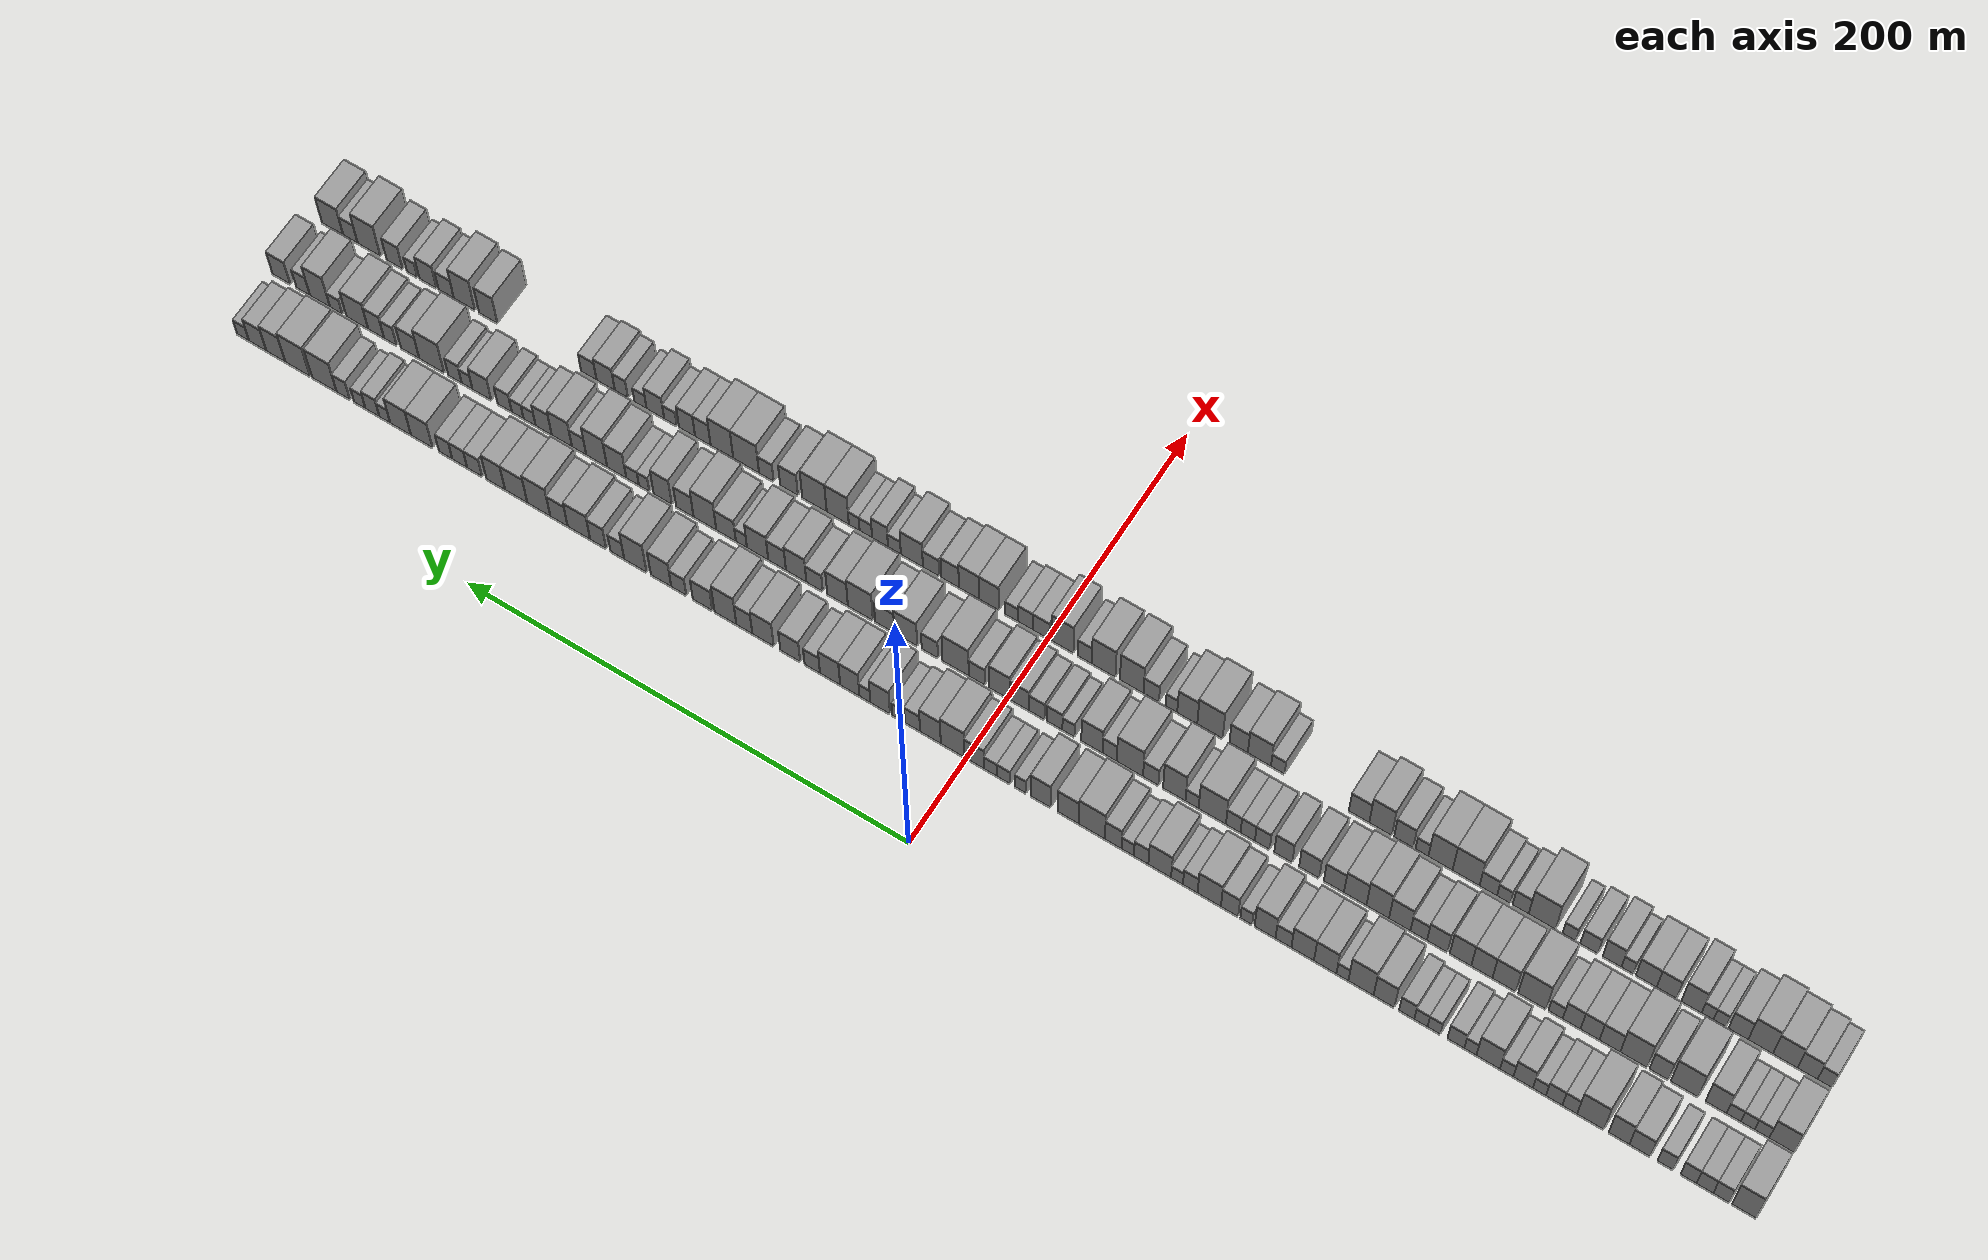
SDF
<sdf version="1.6">
 <world name="default">
  <scene>
   <sky><clouds><speed>12</speed></clouds></sky>
   <ambient>0.4 0.4 0.4 1</ambient>
   <background>0.7 0.7 0.7 1</background>
   <shadows>1</shadows>
  </scene>
  <gravity>0 0 -9.8066</gravity>
  <magnetic_field>6e-06 2.3e-05 -4.2e-05</magnetic_field>
  <physics default="0" name="default_physics" type="ode">
   <ode>
    <solver>
     <type>quick</type>
     <iters>10</iters>
     <sor>1.0</sor>
     <use_dynamic_moi_rescaling>0</use_dynamic_moi_rescaling>
    </solver>
    <constraints>
     <cfm>0</cfm>
     <erp>0.2</erp>
     <contact_max_correcting_vel>100</contact_max_correcting_vel>
     <contact_surface_layer>0.001</contact_surface_layer>
    </constraints>
   </ode>
   <max_step_size>0.004</max_step_size>
   <real_time_factor>1</real_time_factor>
   <real_time_update_rate>250</real_time_update_rate>
  </physics>
  <light name="sun" type="directional">
   <pose>0 0 10 0 0 0</pose>
   <diffuse>0.8 0.8 0.8 1</diffuse>
   <specular>0.2 0.2 0.2 1</specular>
   <attenuation>
    <range>1000</range>
    <constant>0.9</constant>
    <linear>0.01</linear>
    <quadratic>0.001</quadratic>
   </attenuation>
   <direction>-0.5 0.1 -0.9</direction>
  </light>
  <model name="building_1">
   <static>1</static>
   <pose>50.0000 -330.9991 0 0.000000 0.000000 0.000000</pose>
   <link name="link">
    <pose>0 0 12.00 0 0 0</pose>
    <collision name="collision"><geometry><box><size>20.0000 10.0019 24.0000</size></box></geometry></collision>
    <visual name="visual">
     <cast_shadows>0</cast_shadows>
     <geometry><box><size>20.0000 10.0019 24.0000</size></box></geometry>
     <material>
      <script>
       <uri>model://grey_wall/materials/scripts</uri>
       <uri>model://grey_wall/materials/textures</uri>
       <name>vrc/grey_wall</name>
      </script>
     </material>
    </visual>
   </link>
  </model>
  <model name="building_2">
   <static>1</static>
   <pose>50.0000 -321.7026 0 0.000000 0.000000 0.000000</pose>
   <link name="link">
    <pose>0 0 7.50 0 0 0</pose>
    <collision name="collision"><geometry><box><size>20.0000 6.5910 15.0000</size></box></geometry></collision>
    <visual name="visual">
     <cast_shadows>0</cast_shadows>
     <geometry><box><size>20.0000 6.5910 15.0000</size></box></geometry>
     <material>
      <script>
       <uri>model://grey_wall/materials/scripts</uri>
       <uri>model://grey_wall/materials/textures</uri>
       <name>vrc/grey_wall</name>
      </script>
     </material>
    </visual>
   </link>
  </model>
  <model name="building_3">
   <static>1</static>
   <pose>50.0000 -314.9518 0 0.000000 0.000000 0.000000</pose>
   <link name="link">
    <pose>0 0 7.50 0 0 0</pose>
    <collision name="collision"><geometry><box><size>20.0000 6.9107 15.0000</size></box></geometry></collision>
    <visual name="visual">
     <cast_shadows>0</cast_shadows>
     <geometry><box><size>20.0000 6.9107 15.0000</size></box></geometry>
     <material>
      <script>
       <uri>model://grey_wall/materials/scripts</uri>
       <uri>model://grey_wall/materials/textures</uri>
       <name>vrc/grey_wall</name>
      </script>
     </material>
    </visual>
   </link>
  </model>
  <model name="building_4">
   <static>1</static>
   <pose>50.0000 -308.2423 0 0.000000 0.000000 0.000000</pose>
   <link name="link">
    <pose>0 0 7.50 0 0 0</pose>
    <collision name="collision"><geometry><box><size>20.0000 6.5084 15.0000</size></box></geometry></collision>
    <visual name="visual">
     <cast_shadows>0</cast_shadows>
     <geometry><box><size>20.0000 6.5084 15.0000</size></box></geometry>
     <material>
      <script>
       <uri>model://grey_wall/materials/scripts</uri>
       <uri>model://grey_wall/materials/textures</uri>
       <name>vrc/grey_wall</name>
      </script>
     </material>
    </visual>
   </link>
  </model>
  <model name="building_5">
   <static>1</static>
   <pose>50.0000 -298.7529 0 0.000000 0.000000 0.000000</pose>
   <link name="link">
    <pose>0 0 7.50 0 0 0</pose>
    <collision name="collision"><geometry><box><size>20.0000 6.4704 15.0000</size></box></geometry></collision>
    <visual name="visual">
     <cast_shadows>0</cast_shadows>
     <geometry><box><size>20.0000 6.4704 15.0000</size></box></geometry>
     <material>
      <script>
       <uri>model://grey_wall/materials/scripts</uri>
       <uri>model://grey_wall/materials/textures</uri>
       <name>vrc/grey_wall</name>
      </script>
     </material>
    </visual>
   </link>
  </model>
  <model name="building_6">
   <static>1</static>
   <pose>50.0000 -288.2201 0 0.000000 0.000000 0.000000</pose>
   <link name="link">
    <pose>0 0 9.00 0 0 0</pose>
    <collision name="collision"><geometry><box><size>20.0000 8.5954 18.0000</size></box></geometry></collision>
    <visual name="visual">
     <cast_shadows>0</cast_shadows>
     <geometry><box><size>20.0000 8.5954 18.0000</size></box></geometry>
     <material>
      <script>
       <uri>model://grey_wall/materials/scripts</uri>
       <uri>model://grey_wall/materials/textures</uri>
       <name>vrc/grey_wall</name>
      </script>
     </material>
    </visual>
   </link>
  </model>
  <model name="building_7">
   <static>1</static>
   <pose>50.0000 -279.6551 0 0.000000 0.000000 0.000000</pose>
   <link name="link">
    <pose>0 0 10.50 0 0 0</pose>
    <collision name="collision"><geometry><box><size>20.0000 8.5346 21.0000</size></box></geometry></collision>
    <visual name="visual">
     <cast_shadows>0</cast_shadows>
     <geometry><box><size>20.0000 8.5346 21.0000</size></box></geometry>
     <material>
      <script>
       <uri>model://grey_wall/materials/scripts</uri>
       <uri>model://grey_wall/materials/textures</uri>
       <name>vrc/grey_wall</name>
      </script>
     </material>
    </visual>
   </link>
  </model>
  <model name="building_8">
   <static>1</static>
   <pose>50.0000 -267.8186 0 0.000000 0.000000 0.000000</pose>
   <link name="link">
    <pose>0 0 12.00 0 0 0</pose>
    <collision name="collision"><geometry><box><size>20.0000 11.1383 24.0000</size></box></geometry></collision>
    <visual name="visual">
     <cast_shadows>0</cast_shadows>
     <geometry><box><size>20.0000 11.1383 24.0000</size></box></geometry>
     <material>
      <script>
       <uri>model://grey_wall/materials/scripts</uri>
       <uri>model://grey_wall/materials/textures</uri>
       <name>vrc/grey_wall</name>
      </script>
     </material>
    </visual>
   </link>
  </model>
  <model name="building_9">
   <static>1</static>
   <pose>50.0000 -259.2012 0 0.000000 0.000000 0.000000</pose>
   <link name="link">
    <pose>0 0 7.50 0 0 0</pose>
    <collision name="collision"><geometry><box><size>20.0000 6.0966 15.0000</size></box></geometry></collision>
    <visual name="visual">
     <cast_shadows>0</cast_shadows>
     <geometry><box><size>20.0000 6.0966 15.0000</size></box></geometry>
     <material>
      <script>
       <uri>model://grey_wall/materials/scripts</uri>
       <uri>model://grey_wall/materials/textures</uri>
       <name>vrc/grey_wall</name>
      </script>
     </material>
    </visual>
   </link>
  </model>
  <model name="building_10">
   <static>1</static>
   <pose>50.0000 -252.7200 0 0.000000 0.000000 0.000000</pose>
   <link name="link">
    <pose>0 0 7.50 0 0 0</pose>
    <collision name="collision"><geometry><box><size>20.0000 6.8658 15.0000</size></box></geometry></collision>
    <visual name="visual">
     <cast_shadows>0</cast_shadows>
     <geometry><box><size>20.0000 6.8658 15.0000</size></box></geometry>
     <material>
      <script>
       <uri>model://grey_wall/materials/scripts</uri>
       <uri>model://grey_wall/materials/textures</uri>
       <name>vrc/grey_wall</name>
      </script>
     </material>
    </visual>
   </link>
  </model>
  <model name="building_11">
   <static>1</static>
   <pose>50.0000 -246.5598 0 0.000000 0.000000 0.000000</pose>
   <link name="link">
    <pose>0 0 6.00 0 0 0</pose>
    <collision name="collision"><geometry><box><size>20.0000 5.4546 12.0000</size></box></geometry></collision>
    <visual name="visual">
     <cast_shadows>0</cast_shadows>
     <geometry><box><size>20.0000 5.4546 12.0000</size></box></geometry>
     <material>
      <script>
       <uri>model://grey_wall/materials/scripts</uri>
       <uri>model://grey_wall/materials/textures</uri>
       <name>vrc/grey_wall</name>
      </script>
     </material>
    </visual>
   </link>
  </model>
  <model name="building_12">
   <static>1</static>
   <pose>50.0000 -239.7574 0 0.000000 0.000000 0.000000</pose>
   <link name="link">
    <pose>0 0 9.00 0 0 0</pose>
    <collision name="collision"><geometry><box><size>20.0000 8.1502 18.0000</size></box></geometry></collision>
    <visual name="visual">
     <cast_shadows>0</cast_shadows>
     <geometry><box><size>20.0000 8.1502 18.0000</size></box></geometry>
     <material>
      <script>
       <uri>model://grey_wall/materials/scripts</uri>
       <uri>model://grey_wall/materials/textures</uri>
       <name>vrc/grey_wall</name>
      </script>
     </material>
    </visual>
   </link>
  </model>
  <model name="building_13">
   <static>1</static>
   <pose>50.0000 -232.8843 0 0.000000 0.000000 0.000000</pose>
   <link name="link">
    <pose>0 0 6.00 0 0 0</pose>
    <collision name="collision"><geometry><box><size>20.0000 5.5961 12.0000</size></box></geometry></collision>
    <visual name="visual">
     <cast_shadows>0</cast_shadows>
     <geometry><box><size>20.0000 5.5961 12.0000</size></box></geometry>
     <material>
      <script>
       <uri>model://grey_wall/materials/scripts</uri>
       <uri>model://grey_wall/materials/textures</uri>
       <name>vrc/grey_wall</name>
      </script>
     </material>
    </visual>
   </link>
  </model>
  <model name="building_14">
   <static>1</static>
   <pose>50.0000 -225.1341 0 0.000000 0.000000 0.000000</pose>
   <link name="link">
    <pose>0 0 10.50 0 0 0</pose>
    <collision name="collision"><geometry><box><size>20.0000 9.9042 21.0000</size></box></geometry></collision>
    <visual name="visual">
     <cast_shadows>0</cast_shadows>
     <geometry><box><size>20.0000 9.9042 21.0000</size></box></geometry>
     <material>
      <script>
       <uri>model://grey_wall/materials/scripts</uri>
       <uri>model://grey_wall/materials/textures</uri>
       <name>vrc/grey_wall</name>
      </script>
     </material>
    </visual>
   </link>
  </model>
  <model name="building_15">
   <static>1</static>
   <pose>50.0000 -217.6259 0 0.000000 0.000000 0.000000</pose>
   <link name="link">
    <pose>0 0 6.00 0 0 0</pose>
    <collision name="collision"><geometry><box><size>20.0000 5.1122 12.0000</size></box></geometry></collision>
    <visual name="visual">
     <cast_shadows>0</cast_shadows>
     <geometry><box><size>20.0000 5.1122 12.0000</size></box></geometry>
     <material>
      <script>
       <uri>model://grey_wall/materials/scripts</uri>
       <uri>model://grey_wall/materials/textures</uri>
       <name>vrc/grey_wall</name>
      </script>
     </material>
    </visual>
   </link>
  </model>
  <model name="building_16">
   <static>1</static>
   <pose>50.0000 -211.5449 0 0.000000 0.000000 0.000000</pose>
   <link name="link">
    <pose>0 0 7.50 0 0 0</pose>
    <collision name="collision"><geometry><box><size>20.0000 7.0499 15.0000</size></box></geometry></collision>
    <visual name="visual">
     <cast_shadows>0</cast_shadows>
     <geometry><box><size>20.0000 7.0499 15.0000</size></box></geometry>
     <material>
      <script>
       <uri>model://grey_wall/materials/scripts</uri>
       <uri>model://grey_wall/materials/textures</uri>
       <name>vrc/grey_wall</name>
      </script>
     </material>
    </visual>
   </link>
  </model>
  <model name="building_17">
   <static>1</static>
   <pose>50.0000 -202.3055 0 0.000000 0.000000 0.000000</pose>
   <link name="link">
    <pose>0 0 6.00 0 0 0</pose>
    <collision name="collision"><geometry><box><size>20.0000 5.4289 12.0000</size></box></geometry></collision>
    <visual name="visual">
     <cast_shadows>0</cast_shadows>
     <geometry><box><size>20.0000 5.4289 12.0000</size></box></geometry>
     <material>
      <script>
       <uri>model://grey_wall/materials/scripts</uri>
       <uri>model://grey_wall/materials/textures</uri>
       <name>vrc/grey_wall</name>
      </script>
     </material>
    </visual>
   </link>
  </model>
  <model name="building_18">
   <static>1</static>
   <pose>50.0000 -196.8165 0 0.000000 0.000000 0.000000</pose>
   <link name="link">
    <pose>0 0 6.00 0 0 0</pose>
    <collision name="collision"><geometry><box><size>20.0000 5.5491 12.0000</size></box></geometry></collision>
    <visual name="visual">
     <cast_shadows>0</cast_shadows>
     <geometry><box><size>20.0000 5.5491 12.0000</size></box></geometry>
     <material>
      <script>
       <uri>model://grey_wall/materials/scripts</uri>
       <uri>model://grey_wall/materials/textures</uri>
       <name>vrc/grey_wall</name>
      </script>
     </material>
    </visual>
   </link>
  </model>
  <model name="building_19">
   <static>1</static>
   <pose>50.0000 -190.8053 0 0.000000 0.000000 0.000000</pose>
   <link name="link">
    <pose>0 0 7.50 0 0 0</pose>
    <collision name="collision"><geometry><box><size>20.0000 6.4733 15.0000</size></box></geometry></collision>
    <visual name="visual">
     <cast_shadows>0</cast_shadows>
     <geometry><box><size>20.0000 6.4733 15.0000</size></box></geometry>
     <material>
      <script>
       <uri>model://grey_wall/materials/scripts</uri>
       <uri>model://grey_wall/materials/textures</uri>
       <name>vrc/grey_wall</name>
      </script>
     </material>
    </visual>
   </link>
  </model>
  <model name="building_20">
   <static>1</static>
   <pose>50.0000 -181.1631 0 0.000000 0.000000 0.000000</pose>
   <link name="link">
    <pose>0 0 10.50 0 0 0</pose>
    <collision name="collision"><geometry><box><size>20.0000 8.8112 21.0000</size></box></geometry></collision>
    <visual name="visual">
     <cast_shadows>0</cast_shadows>
     <geometry><box><size>20.0000 8.8112 21.0000</size></box></geometry>
     <material>
      <script>
       <uri>model://grey_wall/materials/scripts</uri>
       <uri>model://grey_wall/materials/textures</uri>
       <name>vrc/grey_wall</name>
      </script>
     </material>
    </visual>
   </link>
  </model>
  <model name="building_21">
   <static>1</static>
   <pose>50.0000 -171.3831 0 0.000000 0.000000 0.000000</pose>
   <link name="link">
    <pose>0 0 12.00 0 0 0</pose>
    <collision name="collision"><geometry><box><size>20.0000 10.7487 24.0000</size></box></geometry></collision>
    <visual name="visual">
     <cast_shadows>0</cast_shadows>
     <geometry><box><size>20.0000 10.7487 24.0000</size></box></geometry>
     <material>
      <script>
       <uri>model://grey_wall/materials/scripts</uri>
       <uri>model://grey_wall/materials/textures</uri>
       <name>vrc/grey_wall</name>
      </script>
     </material>
    </visual>
   </link>
  </model>
  <model name="building_22">
   <static>1</static>
   <pose>50.0000 -163.4600 0 0.000000 0.000000 0.000000</pose>
   <link name="link">
    <pose>0 0 6.00 0 0 0</pose>
    <collision name="collision"><geometry><box><size>20.0000 5.0975 12.0000</size></box></geometry></collision>
    <visual name="visual">
     <cast_shadows>0</cast_shadows>
     <geometry><box><size>20.0000 5.0975 12.0000</size></box></geometry>
     <material>
      <script>
       <uri>model://grey_wall/materials/scripts</uri>
       <uri>model://grey_wall/materials/textures</uri>
       <name>vrc/grey_wall</name>
      </script>
     </material>
    </visual>
   </link>
  </model>
  <model name="building_23">
   <static>1</static>
   <pose>50.0000 -156.1194 0 0.000000 0.000000 0.000000</pose>
   <link name="link">
    <pose>0 0 10.50 0 0 0</pose>
    <collision name="collision"><geometry><box><size>20.0000 9.5837 21.0000</size></box></geometry></collision>
    <visual name="visual">
     <cast_shadows>0</cast_shadows>
     <geometry><box><size>20.0000 9.5837 21.0000</size></box></geometry>
     <material>
      <script>
       <uri>model://grey_wall/materials/scripts</uri>
       <uri>model://grey_wall/materials/textures</uri>
       <name>vrc/grey_wall</name>
      </script>
     </material>
    </visual>
   </link>
  </model>
  <model name="building_24">
   <static>1</static>
   <pose>50.0000 -146.5039 0 0.000000 0.000000 0.000000</pose>
   <link name="link">
    <pose>0 0 10.50 0 0 0</pose>
    <collision name="collision"><geometry><box><size>20.0000 9.6473 21.0000</size></box></geometry></collision>
    <visual name="visual">
     <cast_shadows>0</cast_shadows>
     <geometry><box><size>20.0000 9.6473 21.0000</size></box></geometry>
     <material>
      <script>
       <uri>model://grey_wall/materials/scripts</uri>
       <uri>model://grey_wall/materials/textures</uri>
       <name>vrc/grey_wall</name>
      </script>
     </material>
    </visual>
   </link>
  </model>
  <model name="building_25">
   <static>1</static>
   <pose>50.0000 -138.2730 0 0.000000 0.000000 0.000000</pose>
   <link name="link">
    <pose>0 0 7.50 0 0 0</pose>
    <collision name="collision"><geometry><box><size>20.0000 6.8145 15.0000</size></box></geometry></collision>
    <visual name="visual">
     <cast_shadows>0</cast_shadows>
     <geometry><box><size>20.0000 6.8145 15.0000</size></box></geometry>
     <material>
      <script>
       <uri>model://grey_wall/materials/scripts</uri>
       <uri>model://grey_wall/materials/textures</uri>
       <name>vrc/grey_wall</name>
      </script>
     </material>
    </visual>
   </link>
  </model>
  <model name="building_26">
   <static>1</static>
   <pose>50.0000 -130.3590 0 0.000000 0.000000 0.000000</pose>
   <link name="link">
    <pose>0 0 10.50 0 0 0</pose>
    <collision name="collision"><geometry><box><size>20.0000 9.0134 21.0000</size></box></geometry></collision>
    <visual name="visual">
     <cast_shadows>0</cast_shadows>
     <geometry><box><size>20.0000 9.0134 21.0000</size></box></geometry>
     <material>
      <script>
       <uri>model://grey_wall/materials/scripts</uri>
       <uri>model://grey_wall/materials/textures</uri>
       <name>vrc/grey_wall</name>
      </script>
     </material>
    </visual>
   </link>
  </model>
  <model name="building_27">
   <static>1</static>
   <pose>50.0000 -122.3094 0 0.000000 0.000000 0.000000</pose>
   <link name="link">
    <pose>0 0 6.00 0 0 0</pose>
    <collision name="collision"><geometry><box><size>20.0000 5.0859 12.0000</size></box></geometry></collision>
    <visual name="visual">
     <cast_shadows>0</cast_shadows>
     <geometry><box><size>20.0000 5.0859 12.0000</size></box></geometry>
     <material>
      <script>
       <uri>model://grey_wall/materials/scripts</uri>
       <uri>model://grey_wall/materials/textures</uri>
       <name>vrc/grey_wall</name>
      </script>
     </material>
    </visual>
   </link>
  </model>
  <model name="building_28">
   <static>1</static>
   <pose>50.0000 -115.0501 0 0.000000 0.000000 0.000000</pose>
   <link name="link">
    <pose>0 0 9.00 0 0 0</pose>
    <collision name="collision"><geometry><box><size>20.0000 7.4328 18.0000</size></box></geometry></collision>
    <visual name="visual">
     <cast_shadows>0</cast_shadows>
     <geometry><box><size>20.0000 7.4328 18.0000</size></box></geometry>
     <material>
      <script>
       <uri>model://grey_wall/materials/scripts</uri>
       <uri>model://grey_wall/materials/textures</uri>
       <name>vrc/grey_wall</name>
      </script>
     </material>
    </visual>
   </link>
  </model>
  <model name="building_29">
   <static>1</static>
   <pose>50.0000 -106.2806 0 0.000000 0.000000 0.000000</pose>
   <link name="link">
    <pose>0 0 10.50 0 0 0</pose>
    <collision name="collision"><geometry><box><size>20.0000 10.1062 21.0000</size></box></geometry></collision>
    <visual name="visual">
     <cast_shadows>0</cast_shadows>
     <geometry><box><size>20.0000 10.1062 21.0000</size></box></geometry>
     <material>
      <script>
       <uri>model://grey_wall/materials/scripts</uri>
       <uri>model://grey_wall/materials/textures</uri>
       <name>vrc/grey_wall</name>
      </script>
     </material>
    </visual>
   </link>
  </model>
  <model name="building_30">
   <static>1</static>
   <pose>50.0000 -98.0717 0 0.000000 0.000000 0.000000</pose>
   <link name="link">
    <pose>0 0 7.50 0 0 0</pose>
    <collision name="collision"><geometry><box><size>20.0000 6.3116 15.0000</size></box></geometry></collision>
    <visual name="visual">
     <cast_shadows>0</cast_shadows>
     <geometry><box><size>20.0000 6.3116 15.0000</size></box></geometry>
     <material>
      <script>
       <uri>model://grey_wall/materials/scripts</uri>
       <uri>model://grey_wall/materials/textures</uri>
       <name>vrc/grey_wall</name>
      </script>
     </material>
    </visual>
   </link>
  </model>
  <model name="building_31">
   <static>1</static>
   <pose>50.0000 -92.3373 0 0.000000 0.000000 0.000000</pose>
   <link name="link">
    <pose>0 0 6.00 0 0 0</pose>
    <collision name="collision"><geometry><box><size>20.0000 5.1571 12.0000</size></box></geometry></collision>
    <visual name="visual">
     <cast_shadows>0</cast_shadows>
     <geometry><box><size>20.0000 5.1571 12.0000</size></box></geometry>
     <material>
      <script>
       <uri>model://grey_wall/materials/scripts</uri>
       <uri>model://grey_wall/materials/textures</uri>
       <name>vrc/grey_wall</name>
      </script>
     </material>
    </visual>
   </link>
  </model>
  <model name="building_32">
   <static>1</static>
   <pose>50.0000 -84.8233 0 0.000000 0.000000 0.000000</pose>
   <link name="link">
    <pose>0 0 10.50 0 0 0</pose>
    <collision name="collision"><geometry><box><size>20.0000 9.8708 21.0000</size></box></geometry></collision>
    <visual name="visual">
     <cast_shadows>0</cast_shadows>
     <geometry><box><size>20.0000 9.8708 21.0000</size></box></geometry>
     <material>
      <script>
       <uri>model://grey_wall/materials/scripts</uri>
       <uri>model://grey_wall/materials/textures</uri>
       <name>vrc/grey_wall</name>
      </script>
     </material>
    </visual>
   </link>
  </model>
  <model name="building_33">
   <static>1</static>
   <pose>50.0000 -76.7291 0 0.000000 0.000000 0.000000</pose>
   <link name="link">
    <pose>0 0 7.50 0 0 0</pose>
    <collision name="collision"><geometry><box><size>20.0000 6.3176 15.0000</size></box></geometry></collision>
    <visual name="visual">
     <cast_shadows>0</cast_shadows>
     <geometry><box><size>20.0000 6.3176 15.0000</size></box></geometry>
     <material>
      <script>
       <uri>model://grey_wall/materials/scripts</uri>
       <uri>model://grey_wall/materials/textures</uri>
       <name>vrc/grey_wall</name>
      </script>
     </material>
    </visual>
   </link>
  </model>
  <model name="building_34">
   <static>1</static>
   <pose>50.0000 -70.8833 0 0.000000 0.000000 0.000000</pose>
   <link name="link">
    <pose>0 0 6.00 0 0 0</pose>
    <collision name="collision"><geometry><box><size>20.0000 5.3740 12.0000</size></box></geometry></collision>
    <visual name="visual">
     <cast_shadows>0</cast_shadows>
     <geometry><box><size>20.0000 5.3740 12.0000</size></box></geometry>
     <material>
      <script>
       <uri>model://grey_wall/materials/scripts</uri>
       <uri>model://grey_wall/materials/textures</uri>
       <name>vrc/grey_wall</name>
      </script>
     </material>
    </visual>
   </link>
  </model>
  <model name="building_35">
   <static>1</static>
   <pose>50.0000 -64.5480 0 0.000000 0.000000 0.000000</pose>
   <link name="link">
    <pose>0 0 9.00 0 0 0</pose>
    <collision name="collision"><geometry><box><size>20.0000 7.2966 18.0000</size></box></geometry></collision>
    <visual name="visual">
     <cast_shadows>0</cast_shadows>
     <geometry><box><size>20.0000 7.2966 18.0000</size></box></geometry>
     <material>
      <script>
       <uri>model://grey_wall/materials/scripts</uri>
       <uri>model://grey_wall/materials/textures</uri>
       <name>vrc/grey_wall</name>
      </script>
     </material>
    </visual>
   </link>
  </model>
  <model name="building_36">
   <static>1</static>
   <pose>50.0000 -55.1775 0 0.000000 0.000000 0.000000</pose>
   <link name="link">
    <pose>0 0 12.00 0 0 0</pose>
    <collision name="collision"><geometry><box><size>20.0000 11.4444 24.0000</size></box></geometry></collision>
    <visual name="visual">
     <cast_shadows>0</cast_shadows>
     <geometry><box><size>20.0000 11.4444 24.0000</size></box></geometry>
     <material>
      <script>
       <uri>model://grey_wall/materials/scripts</uri>
       <uri>model://grey_wall/materials/textures</uri>
       <name>vrc/grey_wall</name>
      </script>
     </material>
    </visual>
   </link>
  </model>
  <model name="building_37">
   <static>1</static>
   <pose>50.0000 -44.7978 0 0.000000 0.000000 0.000000</pose>
   <link name="link">
    <pose>0 0 10.50 0 0 0</pose>
    <collision name="collision"><geometry><box><size>20.0000 9.3149 21.0000</size></box></geometry></collision>
    <visual name="visual">
     <cast_shadows>0</cast_shadows>
     <geometry><box><size>20.0000 9.3149 21.0000</size></box></geometry>
     <material>
      <script>
       <uri>model://grey_wall/materials/scripts</uri>
       <uri>model://grey_wall/materials/textures</uri>
       <name>vrc/grey_wall</name>
      </script>
     </material>
    </visual>
   </link>
  </model>
  <model name="building_38">
   <static>1</static>
   <pose>50.0000 -32.7465 0 0.000000 0.000000 0.000000</pose>
   <link name="link">
    <pose>0 0 10.50 0 0 0</pose>
    <collision name="collision"><geometry><box><size>20.0000 8.7877 21.0000</size></box></geometry></collision>
    <visual name="visual">
     <cast_shadows>0</cast_shadows>
     <geometry><box><size>20.0000 8.7877 21.0000</size></box></geometry>
     <material>
      <script>
       <uri>model://grey_wall/materials/scripts</uri>
       <uri>model://grey_wall/materials/textures</uri>
       <name>vrc/grey_wall</name>
      </script>
     </material>
    </visual>
   </link>
  </model>
  <model name="building_39">
   <static>1</static>
   <pose>50.0000 -23.8263 0 0.000000 0.000000 0.000000</pose>
   <link name="link">
    <pose>0 0 6.00 0 0 0</pose>
    <collision name="collision"><geometry><box><size>20.0000 5.0527 12.0000</size></box></geometry></collision>
    <visual name="visual">
     <cast_shadows>0</cast_shadows>
     <geometry><box><size>20.0000 5.0527 12.0000</size></box></geometry>
     <material>
      <script>
       <uri>model://grey_wall/materials/scripts</uri>
       <uri>model://grey_wall/materials/textures</uri>
       <name>vrc/grey_wall</name>
      </script>
     </material>
    </visual>
   </link>
  </model>
  <model name="building_40">
   <static>1</static>
   <pose>50.0000 -16.4047 0 0.000000 0.000000 0.000000</pose>
   <link name="link">
    <pose>0 0 6.00 0 0 0</pose>
    <collision name="collision"><geometry><box><size>20.0000 5.7906 12.0000</size></box></geometry></collision>
    <visual name="visual">
     <cast_shadows>0</cast_shadows>
     <geometry><box><size>20.0000 5.7906 12.0000</size></box></geometry>
     <material>
      <script>
       <uri>model://grey_wall/materials/scripts</uri>
       <uri>model://grey_wall/materials/textures</uri>
       <name>vrc/grey_wall</name>
      </script>
     </material>
    </visual>
   </link>
  </model>
  <model name="building_41">
   <static>1</static>
   <pose>50.0000 -10.6505 0 0.000000 0.000000 0.000000</pose>
   <link name="link">
    <pose>0 0 6.00 0 0 0</pose>
    <collision name="collision"><geometry><box><size>20.0000 5.7179 12.0000</size></box></geometry></collision>
    <visual name="visual">
     <cast_shadows>0</cast_shadows>
     <geometry><box><size>20.0000 5.7179 12.0000</size></box></geometry>
     <material>
      <script>
       <uri>model://grey_wall/materials/scripts</uri>
       <uri>model://grey_wall/materials/textures</uri>
       <name>vrc/grey_wall</name>
      </script>
     </material>
    </visual>
   </link>
  </model>
  <model name="building_42">
   <static>1</static>
   <pose>50.0000 -3.3659 0 0.000000 0.000000 0.000000</pose>
   <link name="link">
    <pose>0 0 9.00 0 0 0</pose>
    <collision name="collision"><geometry><box><size>20.0000 8.8512 18.0000</size></box></geometry></collision>
    <visual name="visual">
     <cast_shadows>0</cast_shadows>
     <geometry><box><size>20.0000 8.8512 18.0000</size></box></geometry>
     <material>
      <script>
       <uri>model://grey_wall/materials/scripts</uri>
       <uri>model://grey_wall/materials/textures</uri>
       <name>vrc/grey_wall</name>
      </script>
     </material>
    </visual>
   </link>
  </model>
  <model name="building_43">
   <static>1</static>
   <pose>50.0000 6.2937 0 0.000000 0.000000 0.000000</pose>
   <link name="link">
    <pose>0 0 12.00 0 0 0</pose>
    <collision name="collision"><geometry><box><size>20.0000 10.4679 24.0000</size></box></geometry></collision>
    <visual name="visual">
     <cast_shadows>0</cast_shadows>
     <geometry><box><size>20.0000 10.4679 24.0000</size></box></geometry>
     <material>
      <script>
       <uri>model://grey_wall/materials/scripts</uri>
       <uri>model://grey_wall/materials/textures</uri>
       <name>vrc/grey_wall</name>
      </script>
     </material>
    </visual>
   </link>
  </model>
  <model name="building_44">
   <static>1</static>
   <pose>50.0000 16.1524 0 0.000000 0.000000 0.000000</pose>
   <link name="link">
    <pose>0 0 10.50 0 0 0</pose>
    <collision name="collision"><geometry><box><size>20.0000 9.2495 21.0000</size></box></geometry></collision>
    <visual name="visual">
     <cast_shadows>0</cast_shadows>
     <geometry><box><size>20.0000 9.2495 21.0000</size></box></geometry>
     <material>
      <script>
       <uri>model://grey_wall/materials/scripts</uri>
       <uri>model://grey_wall/materials/textures</uri>
       <name>vrc/grey_wall</name>
      </script>
     </material>
    </visual>
   </link>
  </model>
  <model name="building_45">
   <static>1</static>
   <pose>50.0000 24.1634 0 0.000000 0.000000 0.000000</pose>
   <link name="link">
    <pose>0 0 7.50 0 0 0</pose>
    <collision name="collision"><geometry><box><size>20.0000 6.7723 15.0000</size></box></geometry></collision>
    <visual name="visual">
     <cast_shadows>0</cast_shadows>
     <geometry><box><size>20.0000 6.7723 15.0000</size></box></geometry>
     <material>
      <script>
       <uri>model://grey_wall/materials/scripts</uri>
       <uri>model://grey_wall/materials/textures</uri>
       <name>vrc/grey_wall</name>
      </script>
     </material>
    </visual>
   </link>
  </model>
  <model name="building_46">
   <static>1</static>
   <pose>50.0000 30.4063 0 0.000000 0.000000 0.000000</pose>
   <link name="link">
    <pose>0 0 6.00 0 0 0</pose>
    <collision name="collision"><geometry><box><size>20.0000 5.7136 12.0000</size></box></geometry></collision>
    <visual name="visual">
     <cast_shadows>0</cast_shadows>
     <geometry><box><size>20.0000 5.7136 12.0000</size></box></geometry>
     <material>
      <script>
       <uri>model://grey_wall/materials/scripts</uri>
       <uri>model://grey_wall/materials/textures</uri>
       <name>vrc/grey_wall</name>
      </script>
     </material>
    </visual>
   </link>
  </model>
  <model name="building_47">
   <static>1</static>
   <pose>50.0000 38.6431 0 0.000000 0.000000 0.000000</pose>
   <link name="link">
    <pose>0 0 10.50 0 0 0</pose>
    <collision name="collision"><geometry><box><size>20.0000 8.7599 21.0000</size></box></geometry></collision>
    <visual name="visual">
     <cast_shadows>0</cast_shadows>
     <geometry><box><size>20.0000 8.7599 21.0000</size></box></geometry>
     <material>
      <script>
       <uri>model://grey_wall/materials/scripts</uri>
       <uri>model://grey_wall/materials/textures</uri>
       <name>vrc/grey_wall</name>
      </script>
     </material>
    </visual>
   </link>
  </model>
  <model name="building_48">
   <static>1</static>
   <pose>50.0000 45.4695 0 0.000000 0.000000 0.000000</pose>
   <link name="link">
    <pose>0 0 6.00 0 0 0</pose>
    <collision name="collision"><geometry><box><size>20.0000 4.8929 12.0000</size></box></geometry></collision>
    <visual name="visual">
     <cast_shadows>0</cast_shadows>
     <geometry><box><size>20.0000 4.8929 12.0000</size></box></geometry>
     <material>
      <script>
       <uri>model://grey_wall/materials/scripts</uri>
       <uri>model://grey_wall/materials/textures</uri>
       <name>vrc/grey_wall</name>
      </script>
     </material>
    </visual>
   </link>
  </model>
  <model name="building_49">
   <static>1</static>
   <pose>50.0000 52.2723 0 0.000000 0.000000 0.000000</pose>
   <link name="link">
    <pose>0 0 10.50 0 0 0</pose>
    <collision name="collision"><geometry><box><size>20.0000 8.7125 21.0000</size></box></geometry></collision>
    <visual name="visual">
     <cast_shadows>0</cast_shadows>
     <geometry><box><size>20.0000 8.7125 21.0000</size></box></geometry>
     <material>
      <script>
       <uri>model://grey_wall/materials/scripts</uri>
       <uri>model://grey_wall/materials/textures</uri>
       <name>vrc/grey_wall</name>
      </script>
     </material>
    </visual>
   </link>
  </model>
  <model name="building_50">
   <static>1</static>
   <pose>50.0000 61.1767 0 0.000000 0.000000 0.000000</pose>
   <link name="link">
    <pose>0 0 10.50 0 0 0</pose>
    <collision name="collision"><geometry><box><size>20.0000 9.0963 21.0000</size></box></geometry></collision>
    <visual name="visual">
     <cast_shadows>0</cast_shadows>
     <geometry><box><size>20.0000 9.0963 21.0000</size></box></geometry>
     <material>
      <script>
       <uri>model://grey_wall/materials/scripts</uri>
       <uri>model://grey_wall/materials/textures</uri>
       <name>vrc/grey_wall</name>
      </script>
     </material>
    </visual>
   </link>
  </model>
  <model name="building_51">
   <static>1</static>
   <pose>50.0000 69.1998 0 0.000000 0.000000 0.000000</pose>
   <link name="link">
    <pose>0 0 7.50 0 0 0</pose>
    <collision name="collision"><geometry><box><size>20.0000 6.9499 15.0000</size></box></geometry></collision>
    <visual name="visual">
     <cast_shadows>0</cast_shadows>
     <geometry><box><size>20.0000 6.9499 15.0000</size></box></geometry>
     <material>
      <script>
       <uri>model://grey_wall/materials/scripts</uri>
       <uri>model://grey_wall/materials/textures</uri>
       <name>vrc/grey_wall</name>
      </script>
     </material>
    </visual>
   </link>
  </model>
  <model name="building_52">
   <static>1</static>
   <pose>50.0000 79.1705 0 0.000000 0.000000 0.000000</pose>
   <link name="link">
    <pose>0 0 9.00 0 0 0</pose>
    <collision name="collision"><geometry><box><size>20.0000 8.9916 18.0000</size></box></geometry></collision>
    <visual name="visual">
     <cast_shadows>0</cast_shadows>
     <geometry><box><size>20.0000 8.9916 18.0000</size></box></geometry>
     <material>
      <script>
       <uri>model://grey_wall/materials/scripts</uri>
       <uri>model://grey_wall/materials/textures</uri>
       <name>vrc/grey_wall</name>
      </script>
     </material>
    </visual>
   </link>
  </model>
  <model name="building_53">
   <static>1</static>
   <pose>50.0000 91.5251 0 0.000000 0.000000 0.000000</pose>
   <link name="link">
    <pose>0 0 10.50 0 0 0</pose>
    <collision name="collision"><geometry><box><size>20.0000 9.7175 21.0000</size></box></geometry></collision>
    <visual name="visual">
     <cast_shadows>0</cast_shadows>
     <geometry><box><size>20.0000 9.7175 21.0000</size></box></geometry>
     <material>
      <script>
       <uri>model://grey_wall/materials/scripts</uri>
       <uri>model://grey_wall/materials/textures</uri>
       <name>vrc/grey_wall</name>
      </script>
     </material>
    </visual>
   </link>
  </model>
  <model name="building_54">
   <static>1</static>
   <pose>50.0000 100.0256 0 0.000000 0.000000 0.000000</pose>
   <link name="link">
    <pose>0 0 9.00 0 0 0</pose>
    <collision name="collision"><geometry><box><size>20.0000 7.2835 18.0000</size></box></geometry></collision>
    <visual name="visual">
     <cast_shadows>0</cast_shadows>
     <geometry><box><size>20.0000 7.2835 18.0000</size></box></geometry>
     <material>
      <script>
       <uri>model://grey_wall/materials/scripts</uri>
       <uri>model://grey_wall/materials/textures</uri>
       <name>vrc/grey_wall</name>
      </script>
     </material>
    </visual>
   </link>
  </model>
  <model name="building_55">
   <static>1</static>
   <pose>50.0000 108.6634 0 0.000000 0.000000 0.000000</pose>
   <link name="link">
    <pose>0 0 12.00 0 0 0</pose>
    <collision name="collision"><geometry><box><size>20.0000 9.9921 24.0000</size></box></geometry></collision>
    <visual name="visual">
     <cast_shadows>0</cast_shadows>
     <geometry><box><size>20.0000 9.9921 24.0000</size></box></geometry>
     <material>
      <script>
       <uri>model://grey_wall/materials/scripts</uri>
       <uri>model://grey_wall/materials/textures</uri>
       <name>vrc/grey_wall</name>
      </script>
     </material>
    </visual>
   </link>
  </model>
  <model name="building_56">
   <static>1</static>
   <pose>50.0000 119.1177 0 0.000000 0.000000 0.000000</pose>
   <link name="link">
    <pose>0 0 9.00 0 0 0</pose>
    <collision name="collision"><geometry><box><size>20.0000 8.9166 18.0000</size></box></geometry></collision>
    <visual name="visual">
     <cast_shadows>0</cast_shadows>
     <geometry><box><size>20.0000 8.9166 18.0000</size></box></geometry>
     <material>
      <script>
       <uri>model://grey_wall/materials/scripts</uri>
       <uri>model://grey_wall/materials/textures</uri>
       <name>vrc/grey_wall</name>
      </script>
     </material>
    </visual>
   </link>
  </model>
  <model name="building_57">
   <static>1</static>
   <pose>50.0000 130.0279 0 0.000000 0.000000 0.000000</pose>
   <link name="link">
    <pose>0 0 7.50 0 0 0</pose>
    <collision name="collision"><geometry><box><size>20.0000 6.9039 15.0000</size></box></geometry></collision>
    <visual name="visual">
     <cast_shadows>0</cast_shadows>
     <geometry><box><size>20.0000 6.9039 15.0000</size></box></geometry>
     <material>
      <script>
       <uri>model://grey_wall/materials/scripts</uri>
       <uri>model://grey_wall/materials/textures</uri>
       <name>vrc/grey_wall</name>
      </script>
     </material>
    </visual>
   </link>
  </model>
  <model name="building_58">
   <static>1</static>
   <pose>50.0000 138.1656 0 0.000000 0.000000 0.000000</pose>
   <link name="link">
    <pose>0 0 10.50 0 0 0</pose>
    <collision name="collision"><geometry><box><size>20.0000 9.3716 21.0000</size></box></geometry></collision>
    <visual name="visual">
     <cast_shadows>0</cast_shadows>
     <geometry><box><size>20.0000 9.3716 21.0000</size></box></geometry>
     <material>
      <script>
       <uri>model://grey_wall/materials/scripts</uri>
       <uri>model://grey_wall/materials/textures</uri>
       <name>vrc/grey_wall</name>
      </script>
     </material>
    </visual>
   </link>
  </model>
  <model name="building_59">
   <static>1</static>
   <pose>50.0000 150.0005 0 0.000000 0.000000 0.000000</pose>
   <link name="link">
    <pose>0 0 12.00 0 0 0</pose>
    <collision name="collision"><geometry><box><size>20.0000 10.2981 24.0000</size></box></geometry></collision>
    <visual name="visual">
     <cast_shadows>0</cast_shadows>
     <geometry><box><size>20.0000 10.2981 24.0000</size></box></geometry>
     <material>
      <script>
       <uri>model://grey_wall/materials/scripts</uri>
       <uri>model://grey_wall/materials/textures</uri>
       <name>vrc/grey_wall</name>
      </script>
     </material>
    </visual>
   </link>
  </model>
  <model name="building_60">
   <static>1</static>
   <pose>50.0000 158.3060 0 0.000000 0.000000 0.000000</pose>
   <link name="link">
    <pose>0 0 7.50 0 0 0</pose>
    <collision name="collision"><geometry><box><size>20.0000 6.3129 15.0000</size></box></geometry></collision>
    <visual name="visual">
     <cast_shadows>0</cast_shadows>
     <geometry><box><size>20.0000 6.3129 15.0000</size></box></geometry>
     <material>
      <script>
       <uri>model://grey_wall/materials/scripts</uri>
       <uri>model://grey_wall/materials/textures</uri>
       <name>vrc/grey_wall</name>
      </script>
     </material>
    </visual>
   </link>
  </model>
  <model name="building_61">
   <static>1</static>
   <pose>50.0000 167.1661 0 0.000000 0.000000 0.000000</pose>
   <link name="link">
    <pose>0 0 9.00 0 0 0</pose>
    <collision name="collision"><geometry><box><size>20.0000 7.4073 18.0000</size></box></geometry></collision>
    <visual name="visual">
     <cast_shadows>0</cast_shadows>
     <geometry><box><size>20.0000 7.4073 18.0000</size></box></geometry>
     <material>
      <script>
       <uri>model://grey_wall/materials/scripts</uri>
       <uri>model://grey_wall/materials/textures</uri>
       <name>vrc/grey_wall</name>
      </script>
     </material>
    </visual>
   </link>
  </model>
  <model name="building_62">
   <static>1</static>
   <pose>50.0000 176.1148 0 0.000000 0.000000 0.000000</pose>
   <link name="link">
    <pose>0 0 10.50 0 0 0</pose>
    <collision name="collision"><geometry><box><size>20.0000 10.4902 21.0000</size></box></geometry></collision>
    <visual name="visual">
     <cast_shadows>0</cast_shadows>
     <geometry><box><size>20.0000 10.4902 21.0000</size></box></geometry>
     <material>
      <script>
       <uri>model://grey_wall/materials/scripts</uri>
       <uri>model://grey_wall/materials/textures</uri>
       <name>vrc/grey_wall</name>
      </script>
     </material>
    </visual>
   </link>
  </model>
  <model name="building_63">
   <static>1</static>
   <pose>50.0000 185.3982 0 0.000000 0.000000 0.000000</pose>
   <link name="link">
    <pose>0 0 9.00 0 0 0</pose>
    <collision name="collision"><geometry><box><size>20.0000 8.0765 18.0000</size></box></geometry></collision>
    <visual name="visual">
     <cast_shadows>0</cast_shadows>
     <geometry><box><size>20.0000 8.0765 18.0000</size></box></geometry>
     <material>
      <script>
       <uri>model://grey_wall/materials/scripts</uri>
       <uri>model://grey_wall/materials/textures</uri>
       <name>vrc/grey_wall</name>
      </script>
     </material>
    </visual>
   </link>
  </model>
  <model name="building_64">
   <static>1</static>
   <pose>50.0000 194.7967 0 0.000000 0.000000 0.000000</pose>
   <link name="link">
    <pose>0 0 12.00 0 0 0</pose>
    <collision name="collision"><geometry><box><size>20.0000 10.7207 24.0000</size></box></geometry></collision>
    <visual name="visual">
     <cast_shadows>0</cast_shadows>
     <geometry><box><size>20.0000 10.7207 24.0000</size></box></geometry>
     <material>
      <script>
       <uri>model://grey_wall/materials/scripts</uri>
       <uri>model://grey_wall/materials/textures</uri>
       <name>vrc/grey_wall</name>
      </script>
     </material>
    </visual>
   </link>
  </model>
  <model name="building_65">
   <static>1</static>
   <pose>50.0000 205.3637 0 0.000000 0.000000 0.000000</pose>
   <link name="link">
    <pose>0 0 10.50 0 0 0</pose>
    <collision name="collision"><geometry><box><size>20.0000 10.4133 21.0000</size></box></geometry></collision>
    <visual name="visual">
     <cast_shadows>0</cast_shadows>
     <geometry><box><size>20.0000 10.4133 21.0000</size></box></geometry>
     <material>
      <script>
       <uri>model://grey_wall/materials/scripts</uri>
       <uri>model://grey_wall/materials/textures</uri>
       <name>vrc/grey_wall</name>
      </script>
     </material>
    </visual>
   </link>
  </model>
  <model name="building_66">
   <static>1</static>
   <pose>50.0000 214.9520 0 0.000000 0.000000 0.000000</pose>
   <link name="link">
    <pose>0 0 10.50 0 0 0</pose>
    <collision name="collision"><geometry><box><size>20.0000 8.7633 21.0000</size></box></geometry></collision>
    <visual name="visual">
     <cast_shadows>0</cast_shadows>
     <geometry><box><size>20.0000 8.7633 21.0000</size></box></geometry>
     <material>
      <script>
       <uri>model://grey_wall/materials/scripts</uri>
       <uri>model://grey_wall/materials/textures</uri>
       <name>vrc/grey_wall</name>
      </script>
     </material>
    </visual>
   </link>
  </model>
  <model name="building_67">
   <static>1</static>
   <pose>50.0000 224.8549 0 0.000000 0.000000 0.000000</pose>
   <link name="link">
    <pose>0 0 7.50 0 0 0</pose>
    <collision name="collision"><geometry><box><size>20.0000 7.0425 15.0000</size></box></geometry></collision>
    <visual name="visual">
     <cast_shadows>0</cast_shadows>
     <geometry><box><size>20.0000 7.0425 15.0000</size></box></geometry>
     <material>
      <script>
       <uri>model://grey_wall/materials/scripts</uri>
       <uri>model://grey_wall/materials/textures</uri>
       <name>vrc/grey_wall</name>
      </script>
     </material>
    </visual>
   </link>
  </model>
  <model name="building_68">
   <static>1</static>
   <pose>50.0000 231.8594 0 0.000000 0.000000 0.000000</pose>
   <link name="link">
    <pose>0 0 7.50 0 0 0</pose>
    <collision name="collision"><geometry><box><size>20.0000 6.9664 15.0000</size></box></geometry></collision>
    <visual name="visual">
     <cast_shadows>0</cast_shadows>
     <geometry><box><size>20.0000 6.9664 15.0000</size></box></geometry>
     <material>
      <script>
       <uri>model://grey_wall/materials/scripts</uri>
       <uri>model://grey_wall/materials/textures</uri>
       <name>vrc/grey_wall</name>
      </script>
     </material>
    </visual>
   </link>
  </model>
  <model name="building_69">
   <static>1</static>
   <pose>50.0000 238.4958 0 0.000000 0.000000 0.000000</pose>
   <link name="link">
    <pose>0 0 7.50 0 0 0</pose>
    <collision name="collision"><geometry><box><size>20.0000 6.3065 15.0000</size></box></geometry></collision>
    <visual name="visual">
     <cast_shadows>0</cast_shadows>
     <geometry><box><size>20.0000 6.3065 15.0000</size></box></geometry>
     <material>
      <script>
       <uri>model://grey_wall/materials/scripts</uri>
       <uri>model://grey_wall/materials/textures</uri>
       <name>vrc/grey_wall</name>
      </script>
     </material>
    </visual>
   </link>
  </model>
  <model name="building_70">
   <static>1</static>
   <pose>50.0000 249.7604 0 0.000000 0.000000 0.000000</pose>
   <link name="link">
    <pose>0 0 10.50 0 0 0</pose>
    <collision name="collision"><geometry><box><size>20.0000 10.2226 21.0000</size></box></geometry></collision>
    <visual name="visual">
     <cast_shadows>0</cast_shadows>
     <geometry><box><size>20.0000 10.2226 21.0000</size></box></geometry>
     <material>
      <script>
       <uri>model://grey_wall/materials/scripts</uri>
       <uri>model://grey_wall/materials/textures</uri>
       <name>vrc/grey_wall</name>
      </script>
     </material>
    </visual>
   </link>
  </model>
  <model name="building_71">
   <static>1</static>
   <pose>50.0000 259.7965 0 0.000000 0.000000 0.000000</pose>
   <link name="link">
    <pose>0 0 10.50 0 0 0</pose>
    <collision name="collision"><geometry><box><size>20.0000 9.8497 21.0000</size></box></geometry></collision>
    <visual name="visual">
     <cast_shadows>0</cast_shadows>
     <geometry><box><size>20.0000 9.8497 21.0000</size></box></geometry>
     <material>
      <script>
       <uri>model://grey_wall/materials/scripts</uri>
       <uri>model://grey_wall/materials/textures</uri>
       <name>vrc/grey_wall</name>
      </script>
     </material>
    </visual>
   </link>
  </model>
  <model name="building_72">
   <static>1</static>
   <pose>50.0000 267.2616 0 0.000000 0.000000 0.000000</pose>
   <link name="link">
    <pose>0 0 6.00 0 0 0</pose>
    <collision name="collision"><geometry><box><size>20.0000 5.0805 12.0000</size></box></geometry></collision>
    <visual name="visual">
     <cast_shadows>0</cast_shadows>
     <geometry><box><size>20.0000 5.0805 12.0000</size></box></geometry>
     <material>
      <script>
       <uri>model://grey_wall/materials/scripts</uri>
       <uri>model://grey_wall/materials/textures</uri>
       <name>vrc/grey_wall</name>
      </script>
     </material>
    </visual>
   </link>
  </model>
  <model name="building_73">
   <static>1</static>
   <pose>50.0000 273.1415 0 0.000000 0.000000 0.000000</pose>
   <link name="link">
    <pose>0 0 7.50 0 0 0</pose>
    <collision name="collision"><geometry><box><size>20.0000 6.6795 15.0000</size></box></geometry></collision>
    <visual name="visual">
     <cast_shadows>0</cast_shadows>
     <geometry><box><size>20.0000 6.6795 15.0000</size></box></geometry>
     <material>
      <script>
       <uri>model://grey_wall/materials/scripts</uri>
       <uri>model://grey_wall/materials/textures</uri>
       <name>vrc/grey_wall</name>
      </script>
     </material>
    </visual>
   </link>
  </model>
  <model name="building_74">
   <static>1</static>
   <pose>50.0000 279.1831 0 0.000000 0.000000 0.000000</pose>
   <link name="link">
    <pose>0 0 6.00 0 0 0</pose>
    <collision name="collision"><geometry><box><size>20.0000 5.4036 12.0000</size></box></geometry></collision>
    <visual name="visual">
     <cast_shadows>0</cast_shadows>
     <geometry><box><size>20.0000 5.4036 12.0000</size></box></geometry>
     <material>
      <script>
       <uri>model://grey_wall/materials/scripts</uri>
       <uri>model://grey_wall/materials/textures</uri>
       <name>vrc/grey_wall</name>
      </script>
     </material>
    </visual>
   </link>
  </model>
  <model name="building_75">
   <static>1</static>
   <pose>50.0000 287.0433 0 0.000000 0.000000 0.000000</pose>
   <link name="link">
    <pose>0 0 7.50 0 0 0</pose>
    <collision name="collision"><geometry><box><size>20.0000 6.3169 15.0000</size></box></geometry></collision>
    <visual name="visual">
     <cast_shadows>0</cast_shadows>
     <geometry><box><size>20.0000 6.3169 15.0000</size></box></geometry>
     <material>
      <script>
       <uri>model://grey_wall/materials/scripts</uri>
       <uri>model://grey_wall/materials/textures</uri>
       <name>vrc/grey_wall</name>
      </script>
     </material>
    </visual>
   </link>
  </model>
  <model name="building_76">
   <static>1</static>
   <pose>50.0000 296.0653 0 0.000000 0.000000 0.000000</pose>
   <link name="link">
    <pose>0 0 12.00 0 0 0</pose>
    <collision name="collision"><geometry><box><size>20.0000 11.7271 24.0000</size></box></geometry></collision>
    <visual name="visual">
     <cast_shadows>0</cast_shadows>
     <geometry><box><size>20.0000 11.7271 24.0000</size></box></geometry>
     <material>
      <script>
       <uri>model://grey_wall/materials/scripts</uri>
       <uri>model://grey_wall/materials/textures</uri>
       <name>vrc/grey_wall</name>
      </script>
     </material>
    </visual>
   </link>
  </model>
  <model name="building_77">
   <static>1</static>
   <pose>50.0000 308.8688 0 0.000000 0.000000 0.000000</pose>
   <link name="link">
    <pose>0 0 12.00 0 0 0</pose>
    <collision name="collision"><geometry><box><size>20.0000 11.8798 24.0000</size></box></geometry></collision>
    <visual name="visual">
     <cast_shadows>0</cast_shadows>
     <geometry><box><size>20.0000 11.8798 24.0000</size></box></geometry>
     <material>
      <script>
       <uri>model://grey_wall/materials/scripts</uri>
       <uri>model://grey_wall/materials/textures</uri>
       <name>vrc/grey_wall</name>
      </script>
     </material>
    </visual>
   </link>
  </model>
  <model name="building_78">
   <static>1</static>
   <pose>50.0000 319.3805 0 0.000000 0.000000 0.000000</pose>
   <link name="link">
    <pose>0 0 10.50 0 0 0</pose>
    <collision name="collision"><geometry><box><size>20.0000 9.1436 21.0000</size></box></geometry></collision>
    <visual name="visual">
     <cast_shadows>0</cast_shadows>
     <geometry><box><size>20.0000 9.1436 21.0000</size></box></geometry>
     <material>
      <script>
       <uri>model://grey_wall/materials/scripts</uri>
       <uri>model://grey_wall/materials/textures</uri>
       <name>vrc/grey_wall</name>
      </script>
     </material>
    </visual>
   </link>
  </model>
  <model name="building_79">
   <static>1</static>
   <pose>50.0000 328.1039 0 0.000000 0.000000 0.000000</pose>
   <link name="link">
    <pose>0 0 9.00 0 0 0</pose>
    <collision name="collision"><geometry><box><size>20.0000 8.3032 18.0000</size></box></geometry></collision>
    <visual name="visual">
     <cast_shadows>0</cast_shadows>
     <geometry><box><size>20.0000 8.3032 18.0000</size></box></geometry>
     <material>
      <script>
       <uri>model://grey_wall/materials/scripts</uri>
       <uri>model://grey_wall/materials/textures</uri>
       <name>vrc/grey_wall</name>
      </script>
     </material>
    </visual>
   </link>
  </model>
  <model name="building_80">
   <static>1</static>
   <pose>50.0000 335.1193 0 0.000000 0.000000 0.000000</pose>
   <link name="link">
    <pose>0 0 6.00 0 0 0</pose>
    <collision name="collision"><geometry><box><size>20.0000 5.7276 12.0000</size></box></geometry></collision>
    <visual name="visual">
     <cast_shadows>0</cast_shadows>
     <geometry><box><size>20.0000 5.7276 12.0000</size></box></geometry>
     <material>
      <script>
       <uri>model://grey_wall/materials/scripts</uri>
       <uri>model://grey_wall/materials/textures</uri>
       <name>vrc/grey_wall</name>
      </script>
     </material>
    </visual>
   </link>
  </model>
  <model name="building_81">
   <static>1</static>
   <pose>79.0000 -330.8265 0 0.000000 0.000000 0.000000</pose>
   <link name="link">
    <pose>0 0 10.50 0 0 0</pose>
    <collision name="collision"><geometry><box><size>20.0000 10.3471 21.0000</size></box></geometry></collision>
    <visual name="visual">
     <cast_shadows>0</cast_shadows>
     <geometry><box><size>20.0000 10.3471 21.0000</size></box></geometry>
     <material>
      <script>
       <uri>model://grey_wall/materials/scripts</uri>
       <uri>model://grey_wall/materials/textures</uri>
       <name>vrc/grey_wall</name>
      </script>
     </material>
    </visual>
   </link>
  </model>
  <model name="building_82">
   <static>1</static>
   <pose>79.0000 -322.6670 0 0.000000 0.000000 0.000000</pose>
   <link name="link">
    <pose>0 0 6.00 0 0 0</pose>
    <collision name="collision"><geometry><box><size>20.0000 5.9719 12.0000</size></box></geometry></collision>
    <visual name="visual">
     <cast_shadows>0</cast_shadows>
     <geometry><box><size>20.0000 5.9719 12.0000</size></box></geometry>
     <material>
      <script>
       <uri>model://grey_wall/materials/scripts</uri>
       <uri>model://grey_wall/materials/textures</uri>
       <name>vrc/grey_wall</name>
      </script>
     </material>
    </visual>
   </link>
  </model>
  <model name="building_83">
   <static>1</static>
   <pose>79.0000 -316.8308 0 0.000000 0.000000 0.000000</pose>
   <link name="link">
    <pose>0 0 6.00 0 0 0</pose>
    <collision name="collision"><geometry><box><size>20.0000 5.7003 12.0000</size></box></geometry></collision>
    <visual name="visual">
     <cast_shadows>0</cast_shadows>
     <geometry><box><size>20.0000 5.7003 12.0000</size></box></geometry>
     <material>
      <script>
       <uri>model://grey_wall/materials/scripts</uri>
       <uri>model://grey_wall/materials/textures</uri>
       <name>vrc/grey_wall</name>
      </script>
     </material>
    </visual>
   </link>
  </model>
  <model name="building_84">
   <static>1</static>
   <pose>79.0000 -311.0327 0 0.000000 0.000000 0.000000</pose>
   <link name="link">
    <pose>0 0 6.00 0 0 0</pose>
    <collision name="collision"><geometry><box><size>20.0000 5.8959 12.0000</size></box></geometry></collision>
    <visual name="visual">
     <cast_shadows>0</cast_shadows>
     <geometry><box><size>20.0000 5.8959 12.0000</size></box></geometry>
     <material>
      <script>
       <uri>model://grey_wall/materials/scripts</uri>
       <uri>model://grey_wall/materials/textures</uri>
       <name>vrc/grey_wall</name>
      </script>
     </material>
    </visual>
   </link>
  </model>
  <model name="building_85">
   <static>1</static>
   <pose>79.0000 -303.7470 0 0.000000 0.000000 0.000000</pose>
   <link name="link">
    <pose>0 0 10.50 0 0 0</pose>
    <collision name="collision"><geometry><box><size>20.0000 8.6756 21.0000</size></box></geometry></collision>
    <visual name="visual">
     <cast_shadows>0</cast_shadows>
     <geometry><box><size>20.0000 8.6756 21.0000</size></box></geometry>
     <material>
      <script>
       <uri>model://grey_wall/materials/scripts</uri>
       <uri>model://grey_wall/materials/textures</uri>
       <name>vrc/grey_wall</name>
      </script>
     </material>
    </visual>
   </link>
  </model>
  <model name="building_86">
   <static>1</static>
   <pose>79.0000 -290.7363 0 0.000000 0.000000 0.000000</pose>
   <link name="link">
    <pose>0 0 12.00 0 0 0</pose>
    <collision name="collision"><geometry><box><size>20.0000 11.3456 24.0000</size></box></geometry></collision>
    <visual name="visual">
     <cast_shadows>0</cast_shadows>
     <geometry><box><size>20.0000 11.3456 24.0000</size></box></geometry>
     <material>
      <script>
       <uri>model://grey_wall/materials/scripts</uri>
       <uri>model://grey_wall/materials/textures</uri>
       <name>vrc/grey_wall</name>
      </script>
     </material>
    </visual>
   </link>
  </model>
  <model name="building_87">
   <static>1</static>
   <pose>79.0000 -280.1442 0 0.000000 0.000000 0.000000</pose>
   <link name="link">
    <pose>0 0 9.00 0 0 0</pose>
    <collision name="collision"><geometry><box><size>20.0000 7.8387 18.0000</size></box></geometry></collision>
    <visual name="visual">
     <cast_shadows>0</cast_shadows>
     <geometry><box><size>20.0000 7.8387 18.0000</size></box></geometry>
     <material>
      <script>
       <uri>model://grey_wall/materials/scripts</uri>
       <uri>model://grey_wall/materials/textures</uri>
       <name>vrc/grey_wall</name>
      </script>
     </material>
    </visual>
   </link>
  </model>
  <model name="building_88">
   <static>1</static>
   <pose>79.0000 -269.6344 0 0.000000 0.000000 0.000000</pose>
   <link name="link">
    <pose>0 0 12.00 0 0 0</pose>
    <collision name="collision"><geometry><box><size>20.0000 11.1810 24.0000</size></box></geometry></collision>
    <visual name="visual">
     <cast_shadows>0</cast_shadows>
     <geometry><box><size>20.0000 11.1810 24.0000</size></box></geometry>
     <material>
      <script>
       <uri>model://grey_wall/materials/scripts</uri>
       <uri>model://grey_wall/materials/textures</uri>
       <name>vrc/grey_wall</name>
      </script>
     </material>
    </visual>
   </link>
  </model>
  <model name="building_89">
   <static>1</static>
   <pose>79.0000 -259.7073 0 0.000000 0.000000 0.000000</pose>
   <link name="link">
    <pose>0 0 9.00 0 0 0</pose>
    <collision name="collision"><geometry><box><size>20.0000 8.6731 18.0000</size></box></geometry></collision>
    <visual name="visual">
     <cast_shadows>0</cast_shadows>
     <geometry><box><size>20.0000 8.6731 18.0000</size></box></geometry>
     <material>
      <script>
       <uri>model://grey_wall/materials/scripts</uri>
       <uri>model://grey_wall/materials/textures</uri>
       <name>vrc/grey_wall</name>
      </script>
     </material>
    </visual>
   </link>
  </model>
  <model name="building_90">
   <static>1</static>
   <pose>79.0000 -251.4122 0 0.000000 0.000000 0.000000</pose>
   <link name="link">
    <pose>0 0 9.00 0 0 0</pose>
    <collision name="collision"><geometry><box><size>20.0000 7.9172 18.0000</size></box></geometry></collision>
    <visual name="visual">
     <cast_shadows>0</cast_shadows>
     <geometry><box><size>20.0000 7.9172 18.0000</size></box></geometry>
     <material>
      <script>
       <uri>model://grey_wall/materials/scripts</uri>
       <uri>model://grey_wall/materials/textures</uri>
       <name>vrc/grey_wall</name>
      </script>
     </material>
    </visual>
   </link>
  </model>
  <model name="building_91">
   <static>1</static>
   <pose>79.0000 -243.7211 0 0.000000 0.000000 0.000000</pose>
   <link name="link">
    <pose>0 0 9.00 0 0 0</pose>
    <collision name="collision"><geometry><box><size>20.0000 7.4650 18.0000</size></box></geometry></collision>
    <visual name="visual">
     <cast_shadows>0</cast_shadows>
     <geometry><box><size>20.0000 7.4650 18.0000</size></box></geometry>
     <material>
      <script>
       <uri>model://grey_wall/materials/scripts</uri>
       <uri>model://grey_wall/materials/textures</uri>
       <name>vrc/grey_wall</name>
      </script>
     </material>
    </visual>
   </link>
  </model>
  <model name="building_92">
   <static>1</static>
   <pose>79.0000 -236.9949 0 0.000000 0.000000 0.000000</pose>
   <link name="link">
    <pose>0 0 6.00 0 0 0</pose>
    <collision name="collision"><geometry><box><size>20.0000 5.9873 12.0000</size></box></geometry></collision>
    <visual name="visual">
     <cast_shadows>0</cast_shadows>
     <geometry><box><size>20.0000 5.9873 12.0000</size></box></geometry>
     <material>
      <script>
       <uri>model://grey_wall/materials/scripts</uri>
       <uri>model://grey_wall/materials/textures</uri>
       <name>vrc/grey_wall</name>
      </script>
     </material>
    </visual>
   </link>
  </model>
  <model name="building_93">
   <static>1</static>
   <pose>79.0000 -227.1209 0 0.000000 0.000000 0.000000</pose>
   <link name="link">
    <pose>0 0 12.00 0 0 0</pose>
    <collision name="collision"><geometry><box><size>20.0000 11.7606 24.0000</size></box></geometry></collision>
    <visual name="visual">
     <cast_shadows>0</cast_shadows>
     <geometry><box><size>20.0000 11.7606 24.0000</size></box></geometry>
     <material>
      <script>
       <uri>model://grey_wall/materials/scripts</uri>
       <uri>model://grey_wall/materials/textures</uri>
       <name>vrc/grey_wall</name>
      </script>
     </material>
    </visual>
   </link>
  </model>
  <model name="building_94">
   <static>1</static>
   <pose>79.0000 -215.3089 0 0.000000 0.000000 0.000000</pose>
   <link name="link">
    <pose>0 0 10.50 0 0 0</pose>
    <collision name="collision"><geometry><box><size>20.0000 9.8634 21.0000</size></box></geometry></collision>
    <visual name="visual">
     <cast_shadows>0</cast_shadows>
     <geometry><box><size>20.0000 9.8634 21.0000</size></box></geometry>
     <material>
      <script>
       <uri>model://grey_wall/materials/scripts</uri>
       <uri>model://grey_wall/materials/textures</uri>
       <name>vrc/grey_wall</name>
      </script>
     </material>
    </visual>
   </link>
  </model>
  <model name="building_95">
   <static>1</static>
   <pose>79.0000 -205.8949 0 0.000000 0.000000 0.000000</pose>
   <link name="link">
    <pose>0 0 10.50 0 0 0</pose>
    <collision name="collision"><geometry><box><size>20.0000 8.9645 21.0000</size></box></geometry></collision>
    <visual name="visual">
     <cast_shadows>0</cast_shadows>
     <geometry><box><size>20.0000 8.9645 21.0000</size></box></geometry>
     <material>
      <script>
       <uri>model://grey_wall/materials/scripts</uri>
       <uri>model://grey_wall/materials/textures</uri>
       <name>vrc/grey_wall</name>
      </script>
     </material>
    </visual>
   </link>
  </model>
  <model name="building_96">
   <static>1</static>
   <pose>79.0000 -196.8538 0 0.000000 0.000000 0.000000</pose>
   <link name="link">
    <pose>0 0 10.50 0 0 0</pose>
    <collision name="collision"><geometry><box><size>20.0000 9.1178 21.0000</size></box></geometry></collision>
    <visual name="visual">
     <cast_shadows>0</cast_shadows>
     <geometry><box><size>20.0000 9.1178 21.0000</size></box></geometry>
     <material>
      <script>
       <uri>model://grey_wall/materials/scripts</uri>
       <uri>model://grey_wall/materials/textures</uri>
       <name>vrc/grey_wall</name>
      </script>
     </material>
    </visual>
   </link>
  </model>
  <model name="building_97">
   <static>1</static>
   <pose>79.0000 -186.9628 0 0.000000 0.000000 0.000000</pose>
   <link name="link">
    <pose>0 0 9.00 0 0 0</pose>
    <collision name="collision"><geometry><box><size>20.0000 8.6643 18.0000</size></box></geometry></collision>
    <visual name="visual">
     <cast_shadows>0</cast_shadows>
     <geometry><box><size>20.0000 8.6643 18.0000</size></box></geometry>
     <material>
      <script>
       <uri>model://grey_wall/materials/scripts</uri>
       <uri>model://grey_wall/materials/textures</uri>
       <name>vrc/grey_wall</name>
      </script>
     </material>
    </visual>
   </link>
  </model>
  <model name="building_98">
   <static>1</static>
   <pose>79.0000 -179.0969 0 0.000000 0.000000 0.000000</pose>
   <link name="link">
    <pose>0 0 7.50 0 0 0</pose>
    <collision name="collision"><geometry><box><size>20.0000 7.0674 15.0000</size></box></geometry></collision>
    <visual name="visual">
     <cast_shadows>0</cast_shadows>
     <geometry><box><size>20.0000 7.0674 15.0000</size></box></geometry>
     <material>
      <script>
       <uri>model://grey_wall/materials/scripts</uri>
       <uri>model://grey_wall/materials/textures</uri>
       <name>vrc/grey_wall</name>
      </script>
     </material>
    </visual>
   </link>
  </model>
  <model name="building_99">
   <static>1</static>
   <pose>79.0000 -170.9945 0 0.000000 0.000000 0.000000</pose>
   <link name="link">
    <pose>0 0 10.50 0 0 0</pose>
    <collision name="collision"><geometry><box><size>20.0000 9.1376 21.0000</size></box></geometry></collision>
    <visual name="visual">
     <cast_shadows>0</cast_shadows>
     <geometry><box><size>20.0000 9.1376 21.0000</size></box></geometry>
     <material>
      <script>
       <uri>model://grey_wall/materials/scripts</uri>
       <uri>model://grey_wall/materials/textures</uri>
       <name>vrc/grey_wall</name>
      </script>
     </material>
    </visual>
   </link>
  </model>
  <model name="building_100">
   <static>1</static>
   <pose>79.0000 -161.5759 0 0.000000 0.000000 0.000000</pose>
   <link name="link">
    <pose>0 0 12.00 0 0 0</pose>
    <collision name="collision"><geometry><box><size>20.0000 9.6996 24.0000</size></box></geometry></collision>
    <visual name="visual">
     <cast_shadows>0</cast_shadows>
     <geometry><box><size>20.0000 9.6996 24.0000</size></box></geometry>
     <material>
      <script>
       <uri>model://grey_wall/materials/scripts</uri>
       <uri>model://grey_wall/materials/textures</uri>
       <name>vrc/grey_wall</name>
      </script>
     </material>
    </visual>
   </link>
  </model>
  <model name="building_101">
   <static>1</static>
   <pose>79.0000 -151.9213 0 0.000000 0.000000 0.000000</pose>
   <link name="link">
    <pose>0 0 10.50 0 0 0</pose>
    <collision name="collision"><geometry><box><size>20.0000 9.6097 21.0000</size></box></geometry></collision>
    <visual name="visual">
     <cast_shadows>0</cast_shadows>
     <geometry><box><size>20.0000 9.6097 21.0000</size></box></geometry>
     <material>
      <script>
       <uri>model://grey_wall/materials/scripts</uri>
       <uri>model://grey_wall/materials/textures</uri>
       <name>vrc/grey_wall</name>
      </script>
     </material>
    </visual>
   </link>
  </model>
  <model name="building_102">
   <static>1</static>
   <pose>79.0000 -142.7765 0 0.000000 0.000000 0.000000</pose>
   <link name="link">
    <pose>0 0 9.00 0 0 0</pose>
    <collision name="collision"><geometry><box><size>20.0000 8.6799 18.0000</size></box></geometry></collision>
    <visual name="visual">
     <cast_shadows>0</cast_shadows>
     <geometry><box><size>20.0000 8.6799 18.0000</size></box></geometry>
     <material>
      <script>
       <uri>model://grey_wall/materials/scripts</uri>
       <uri>model://grey_wall/materials/textures</uri>
       <name>vrc/grey_wall</name>
      </script>
     </material>
    </visual>
   </link>
  </model>
  <model name="building_103">
   <static>1</static>
   <pose>79.0000 -132.1159 0 0.000000 0.000000 0.000000</pose>
   <link name="link">
    <pose>0 0 9.00 0 0 0</pose>
    <collision name="collision"><geometry><box><size>20.0000 8.6413 18.0000</size></box></geometry></collision>
    <visual name="visual">
     <cast_shadows>0</cast_shadows>
     <geometry><box><size>20.0000 8.6413 18.0000</size></box></geometry>
     <material>
      <script>
       <uri>model://grey_wall/materials/scripts</uri>
       <uri>model://grey_wall/materials/textures</uri>
       <name>vrc/grey_wall</name>
      </script>
     </material>
    </visual>
   </link>
  </model>
  <model name="building_104">
   <static>1</static>
   <pose>79.0000 -120.9142 0 0.000000 0.000000 0.000000</pose>
   <link name="link">
    <pose>0 0 9.00 0 0 0</pose>
    <collision name="collision"><geometry><box><size>20.0000 7.7621 18.0000</size></box></geometry></collision>
    <visual name="visual">
     <cast_shadows>0</cast_shadows>
     <geometry><box><size>20.0000 7.7621 18.0000</size></box></geometry>
     <material>
      <script>
       <uri>model://grey_wall/materials/scripts</uri>
       <uri>model://grey_wall/materials/textures</uri>
       <name>vrc/grey_wall</name>
      </script>
     </material>
    </visual>
   </link>
  </model>
  <model name="building_105">
   <static>1</static>
   <pose>79.0000 -111.8273 0 0.000000 0.000000 0.000000</pose>
   <link name="link">
    <pose>0 0 7.50 0 0 0</pose>
    <collision name="collision"><geometry><box><size>20.0000 6.4116 15.0000</size></box></geometry></collision>
    <visual name="visual">
     <cast_shadows>0</cast_shadows>
     <geometry><box><size>20.0000 6.4116 15.0000</size></box></geometry>
     <material>
      <script>
       <uri>model://grey_wall/materials/scripts</uri>
       <uri>model://grey_wall/materials/textures</uri>
       <name>vrc/grey_wall</name>
      </script>
     </material>
    </visual>
   </link>
  </model>
  <model name="building_106">
   <static>1</static>
   <pose>79.0000 -105.5062 0 0.000000 0.000000 0.000000</pose>
   <link name="link">
    <pose>0 0 7.50 0 0 0</pose>
    <collision name="collision"><geometry><box><size>20.0000 6.2306 15.0000</size></box></geometry></collision>
    <visual name="visual">
     <cast_shadows>0</cast_shadows>
     <geometry><box><size>20.0000 6.2306 15.0000</size></box></geometry>
     <material>
      <script>
       <uri>model://grey_wall/materials/scripts</uri>
       <uri>model://grey_wall/materials/textures</uri>
       <name>vrc/grey_wall</name>
      </script>
     </material>
    </visual>
   </link>
  </model>
  <model name="building_107">
   <static>1</static>
   <pose>79.0000 -99.2215 0 0.000000 0.000000 0.000000</pose>
   <link name="link">
    <pose>0 0 7.50 0 0 0</pose>
    <collision name="collision"><geometry><box><size>20.0000 6.3388 15.0000</size></box></geometry></collision>
    <visual name="visual">
     <cast_shadows>0</cast_shadows>
     <geometry><box><size>20.0000 6.3388 15.0000</size></box></geometry>
     <material>
      <script>
       <uri>model://grey_wall/materials/scripts</uri>
       <uri>model://grey_wall/materials/textures</uri>
       <name>vrc/grey_wall</name>
      </script>
     </material>
    </visual>
   </link>
  </model>
  <model name="building_108">
   <static>1</static>
   <pose>79.0000 -90.1090 0 0.000000 0.000000 0.000000</pose>
   <link name="link">
    <pose>0 0 12.00 0 0 0</pose>
    <collision name="collision"><geometry><box><size>20.0000 11.8864 24.0000</size></box></geometry></collision>
    <visual name="visual">
     <cast_shadows>0</cast_shadows>
     <geometry><box><size>20.0000 11.8864 24.0000</size></box></geometry>
     <material>
      <script>
       <uri>model://grey_wall/materials/scripts</uri>
       <uri>model://grey_wall/materials/textures</uri>
       <name>vrc/grey_wall</name>
      </script>
     </material>
    </visual>
   </link>
  </model>
  <model name="building_109">
   <static>1</static>
   <pose>79.0000 -81.2857 0 0.000000 0.000000 0.000000</pose>
   <link name="link">
    <pose>0 0 6.00 0 0 0</pose>
    <collision name="collision"><geometry><box><size>20.0000 5.7601 12.0000</size></box></geometry></collision>
    <visual name="visual">
     <cast_shadows>0</cast_shadows>
     <geometry><box><size>20.0000 5.7601 12.0000</size></box></geometry>
     <material>
      <script>
       <uri>model://grey_wall/materials/scripts</uri>
       <uri>model://grey_wall/materials/textures</uri>
       <name>vrc/grey_wall</name>
      </script>
     </material>
    </visual>
   </link>
  </model>
  <model name="building_110">
   <static>1</static>
   <pose>79.0000 -73.5068 0 0.000000 0.000000 0.000000</pose>
   <link name="link">
    <pose>0 0 12.00 0 0 0</pose>
    <collision name="collision"><geometry><box><size>20.0000 9.7977 24.0000</size></box></geometry></collision>
    <visual name="visual">
     <cast_shadows>0</cast_shadows>
     <geometry><box><size>20.0000 9.7977 24.0000</size></box></geometry>
     <material>
      <script>
       <uri>model://grey_wall/materials/scripts</uri>
       <uri>model://grey_wall/materials/textures</uri>
       <name>vrc/grey_wall</name>
      </script>
     </material>
    </visual>
   </link>
  </model>
  <model name="building_111">
   <static>1</static>
   <pose>79.0000 -63.2096 0 0.000000 0.000000 0.000000</pose>
   <link name="link">
    <pose>0 0 7.50 0 0 0</pose>
    <collision name="collision"><geometry><box><size>20.0000 6.7968 15.0000</size></box></geometry></collision>
    <visual name="visual">
     <cast_shadows>0</cast_shadows>
     <geometry><box><size>20.0000 6.7968 15.0000</size></box></geometry>
     <material>
      <script>
       <uri>model://grey_wall/materials/scripts</uri>
       <uri>model://grey_wall/materials/textures</uri>
       <name>vrc/grey_wall</name>
      </script>
     </material>
    </visual>
   </link>
  </model>
  <model name="building_112">
   <static>1</static>
   <pose>79.0000 -54.0190 0 0.000000 0.000000 0.000000</pose>
   <link name="link">
    <pose>0 0 12.00 0 0 0</pose>
    <collision name="collision"><geometry><box><size>20.0000 11.5843 24.0000</size></box></geometry></collision>
    <visual name="visual">
     <cast_shadows>0</cast_shadows>
     <geometry><box><size>20.0000 11.5843 24.0000</size></box></geometry>
     <material>
      <script>
       <uri>model://grey_wall/materials/scripts</uri>
       <uri>model://grey_wall/materials/textures</uri>
       <name>vrc/grey_wall</name>
      </script>
     </material>
    </visual>
   </link>
  </model>
  <model name="building_113">
   <static>1</static>
   <pose>79.0000 -45.1271 0 0.000000 0.000000 0.000000</pose>
   <link name="link">
    <pose>0 0 7.50 0 0 0</pose>
    <collision name="collision"><geometry><box><size>20.0000 6.1996 15.0000</size></box></geometry></collision>
    <visual name="visual">
     <cast_shadows>0</cast_shadows>
     <geometry><box><size>20.0000 6.1996 15.0000</size></box></geometry>
     <material>
      <script>
       <uri>model://grey_wall/materials/scripts</uri>
       <uri>model://grey_wall/materials/textures</uri>
       <name>vrc/grey_wall</name>
      </script>
     </material>
    </visual>
   </link>
  </model>
  <model name="building_114">
   <static>1</static>
   <pose>79.0000 -37.3034 0 0.000000 0.000000 0.000000</pose>
   <link name="link">
    <pose>0 0 10.50 0 0 0</pose>
    <collision name="collision"><geometry><box><size>20.0000 9.4477 21.0000</size></box></geometry></collision>
    <visual name="visual">
     <cast_shadows>0</cast_shadows>
     <geometry><box><size>20.0000 9.4477 21.0000</size></box></geometry>
     <material>
      <script>
       <uri>model://grey_wall/materials/scripts</uri>
       <uri>model://grey_wall/materials/textures</uri>
       <name>vrc/grey_wall</name>
      </script>
     </material>
    </visual>
   </link>
  </model>
  <model name="building_115">
   <static>1</static>
   <pose>79.0000 -26.9018 0 0.000000 0.000000 0.000000</pose>
   <link name="link">
    <pose>0 0 6.00 0 0 0</pose>
    <collision name="collision"><geometry><box><size>20.0000 5.3554 12.0000</size></box></geometry></collision>
    <visual name="visual">
     <cast_shadows>0</cast_shadows>
     <geometry><box><size>20.0000 5.3554 12.0000</size></box></geometry>
     <material>
      <script>
       <uri>model://grey_wall/materials/scripts</uri>
       <uri>model://grey_wall/materials/textures</uri>
       <name>vrc/grey_wall</name>
      </script>
     </material>
    </visual>
   </link>
  </model>
  <model name="building_116">
   <static>1</static>
   <pose>79.0000 -20.7632 0 0.000000 0.000000 0.000000</pose>
   <link name="link">
    <pose>0 0 7.50 0 0 0</pose>
    <collision name="collision"><geometry><box><size>20.0000 6.9219 15.0000</size></box></geometry></collision>
    <visual name="visual">
     <cast_shadows>0</cast_shadows>
     <geometry><box><size>20.0000 6.9219 15.0000</size></box></geometry>
     <material>
      <script>
       <uri>model://grey_wall/materials/scripts</uri>
       <uri>model://grey_wall/materials/textures</uri>
       <name>vrc/grey_wall</name>
      </script>
     </material>
    </visual>
   </link>
  </model>
  <model name="building_117">
   <static>1</static>
   <pose>79.0000 -12.9393 0 0.000000 0.000000 0.000000</pose>
   <link name="link">
    <pose>0 0 7.50 0 0 0</pose>
    <collision name="collision"><geometry><box><size>20.0000 6.7259 15.0000</size></box></geometry></collision>
    <visual name="visual">
     <cast_shadows>0</cast_shadows>
     <geometry><box><size>20.0000 6.7259 15.0000</size></box></geometry>
     <material>
      <script>
       <uri>model://grey_wall/materials/scripts</uri>
       <uri>model://grey_wall/materials/textures</uri>
       <name>vrc/grey_wall</name>
      </script>
     </material>
    </visual>
   </link>
  </model>
  <model name="building_118">
   <static>1</static>
   <pose>79.0000 -5.2491 0 0.000000 0.000000 0.000000</pose>
   <link name="link">
    <pose>0 0 9.00 0 0 0</pose>
    <collision name="collision"><geometry><box><size>20.0000 8.6545 18.0000</size></box></geometry></collision>
    <visual name="visual">
     <cast_shadows>0</cast_shadows>
     <geometry><box><size>20.0000 8.6545 18.0000</size></box></geometry>
     <material>
      <script>
       <uri>model://grey_wall/materials/scripts</uri>
       <uri>model://grey_wall/materials/textures</uri>
       <name>vrc/grey_wall</name>
      </script>
     </material>
    </visual>
   </link>
  </model>
  <model name="building_119">
   <static>1</static>
   <pose>79.0000 3.6770 0 0.000000 0.000000 0.000000</pose>
   <link name="link">
    <pose>0 0 10.50 0 0 0</pose>
    <collision name="collision"><geometry><box><size>20.0000 9.1977 21.0000</size></box></geometry></collision>
    <visual name="visual">
     <cast_shadows>0</cast_shadows>
     <geometry><box><size>20.0000 9.1977 21.0000</size></box></geometry>
     <material>
      <script>
       <uri>model://grey_wall/materials/scripts</uri>
       <uri>model://grey_wall/materials/textures</uri>
       <name>vrc/grey_wall</name>
      </script>
     </material>
    </visual>
   </link>
  </model>
  <model name="building_120">
   <static>1</static>
   <pose>79.0000 13.8615 0 0.000000 0.000000 0.000000</pose>
   <link name="link">
    <pose>0 0 7.50 0 0 0</pose>
    <collision name="collision"><geometry><box><size>20.0000 7.1713 15.0000</size></box></geometry></collision>
    <visual name="visual">
     <cast_shadows>0</cast_shadows>
     <geometry><box><size>20.0000 7.1713 15.0000</size></box></geometry>
     <material>
      <script>
       <uri>model://grey_wall/materials/scripts</uri>
       <uri>model://grey_wall/materials/textures</uri>
       <name>vrc/grey_wall</name>
      </script>
     </material>
    </visual>
   </link>
  </model>
  <model name="building_121">
   <static>1</static>
   <pose>79.0000 23.3644 0 0.000000 0.000000 0.000000</pose>
   <link name="link">
    <pose>0 0 12.00 0 0 0</pose>
    <collision name="collision"><geometry><box><size>20.0000 11.8346 24.0000</size></box></geometry></collision>
    <visual name="visual">
     <cast_shadows>0</cast_shadows>
     <geometry><box><size>20.0000 11.8346 24.0000</size></box></geometry>
     <material>
      <script>
       <uri>model://grey_wall/materials/scripts</uri>
       <uri>model://grey_wall/materials/textures</uri>
       <name>vrc/grey_wall</name>
      </script>
     </material>
    </visual>
   </link>
  </model>
  <model name="building_122">
   <static>1</static>
   <pose>79.0000 34.9454 0 0.000000 0.000000 0.000000</pose>
   <link name="link">
    <pose>0 0 7.50 0 0 0</pose>
    <collision name="collision"><geometry><box><size>20.0000 7.3276 15.0000</size></box></geometry></collision>
    <visual name="visual">
     <cast_shadows>0</cast_shadows>
     <geometry><box><size>20.0000 7.3276 15.0000</size></box></geometry>
     <material>
      <script>
       <uri>model://grey_wall/materials/scripts</uri>
       <uri>model://grey_wall/materials/textures</uri>
       <name>vrc/grey_wall</name>
      </script>
     </material>
    </visual>
   </link>
  </model>
  <model name="building_123">
   <static>1</static>
   <pose>79.0000 45.7378 0 0.000000 0.000000 0.000000</pose>
   <link name="link">
    <pose>0 0 10.50 0 0 0</pose>
    <collision name="collision"><geometry><box><size>20.0000 10.2572 21.0000</size></box></geometry></collision>
    <visual name="visual">
     <cast_shadows>0</cast_shadows>
     <geometry><box><size>20.0000 10.2572 21.0000</size></box></geometry>
     <material>
      <script>
       <uri>model://grey_wall/materials/scripts</uri>
       <uri>model://grey_wall/materials/textures</uri>
       <name>vrc/grey_wall</name>
      </script>
     </material>
    </visual>
   </link>
  </model>
  <model name="building_124">
   <static>1</static>
   <pose>79.0000 55.2541 0 0.000000 0.000000 0.000000</pose>
   <link name="link">
    <pose>0 0 9.00 0 0 0</pose>
    <collision name="collision"><geometry><box><size>20.0000 8.7753 18.0000</size></box></geometry></collision>
    <visual name="visual">
     <cast_shadows>0</cast_shadows>
     <geometry><box><size>20.0000 8.7753 18.0000</size></box></geometry>
     <material>
      <script>
       <uri>model://grey_wall/materials/scripts</uri>
       <uri>model://grey_wall/materials/textures</uri>
       <name>vrc/grey_wall</name>
      </script>
     </material>
    </visual>
   </link>
  </model>
  <model name="building_125">
   <static>1</static>
   <pose>79.0000 66.2986 0 0.000000 0.000000 0.000000</pose>
   <link name="link">
    <pose>0 0 12.00 0 0 0</pose>
    <collision name="collision"><geometry><box><size>20.0000 11.3137 24.0000</size></box></geometry></collision>
    <visual name="visual">
     <cast_shadows>0</cast_shadows>
     <geometry><box><size>20.0000 11.3137 24.0000</size></box></geometry>
     <material>
      <script>
       <uri>model://grey_wall/materials/scripts</uri>
       <uri>model://grey_wall/materials/textures</uri>
       <name>vrc/grey_wall</name>
      </script>
     </material>
    </visual>
   </link>
  </model>
  <model name="building_126">
   <static>1</static>
   <pose>79.0000 76.6638 0 0.000000 0.000000 0.000000</pose>
   <link name="link">
    <pose>0 0 10.50 0 0 0</pose>
    <collision name="collision"><geometry><box><size>20.0000 9.4169 21.0000</size></box></geometry></collision>
    <visual name="visual">
     <cast_shadows>0</cast_shadows>
     <geometry><box><size>20.0000 9.4169 21.0000</size></box></geometry>
     <material>
      <script>
       <uri>model://grey_wall/materials/scripts</uri>
       <uri>model://grey_wall/materials/textures</uri>
       <name>vrc/grey_wall</name>
      </script>
     </material>
    </visual>
   </link>
  </model>
  <model name="building_127">
   <static>1</static>
   <pose>79.0000 87.0997 0 0.000000 0.000000 0.000000</pose>
   <link name="link">
    <pose>0 0 7.50 0 0 0</pose>
    <collision name="collision"><geometry><box><size>20.0000 7.4548 15.0000</size></box></geometry></collision>
    <visual name="visual">
     <cast_shadows>0</cast_shadows>
     <geometry><box><size>20.0000 7.4548 15.0000</size></box></geometry>
     <material>
      <script>
       <uri>model://grey_wall/materials/scripts</uri>
       <uri>model://grey_wall/materials/textures</uri>
       <name>vrc/grey_wall</name>
      </script>
     </material>
    </visual>
   </link>
  </model>
  <model name="building_128">
   <static>1</static>
   <pose>79.0000 95.5127 0 0.000000 0.000000 0.000000</pose>
   <link name="link">
    <pose>0 0 10.50 0 0 0</pose>
    <collision name="collision"><geometry><box><size>20.0000 9.3712 21.0000</size></box></geometry></collision>
    <visual name="visual">
     <cast_shadows>0</cast_shadows>
     <geometry><box><size>20.0000 9.3712 21.0000</size></box></geometry>
     <material>
      <script>
       <uri>model://grey_wall/materials/scripts</uri>
       <uri>model://grey_wall/materials/textures</uri>
       <name>vrc/grey_wall</name>
      </script>
     </material>
    </visual>
   </link>
  </model>
  <model name="building_129">
   <static>1</static>
   <pose>79.0000 104.2390 0 0.000000 0.000000 0.000000</pose>
   <link name="link">
    <pose>0 0 9.00 0 0 0</pose>
    <collision name="collision"><geometry><box><size>20.0000 8.0815 18.0000</size></box></geometry></collision>
    <visual name="visual">
     <cast_shadows>0</cast_shadows>
     <geometry><box><size>20.0000 8.0815 18.0000</size></box></geometry>
     <material>
      <script>
       <uri>model://grey_wall/materials/scripts</uri>
       <uri>model://grey_wall/materials/textures</uri>
       <name>vrc/grey_wall</name>
      </script>
     </material>
    </visual>
   </link>
  </model>
  <model name="building_130">
   <static>1</static>
   <pose>79.0000 113.1533 0 0.000000 0.000000 0.000000</pose>
   <link name="link">
    <pose>0 0 10.50 0 0 0</pose>
    <collision name="collision"><geometry><box><size>20.0000 9.7470 21.0000</size></box></geometry></collision>
    <visual name="visual">
     <cast_shadows>0</cast_shadows>
     <geometry><box><size>20.0000 9.7470 21.0000</size></box></geometry>
     <material>
      <script>
       <uri>model://grey_wall/materials/scripts</uri>
       <uri>model://grey_wall/materials/textures</uri>
       <name>vrc/grey_wall</name>
      </script>
     </material>
    </visual>
   </link>
  </model>
  <model name="building_131">
   <static>1</static>
   <pose>79.0000 120.5847 0 0.000000 0.000000 0.000000</pose>
   <link name="link">
    <pose>0 0 6.00 0 0 0</pose>
    <collision name="collision"><geometry><box><size>20.0000 5.1157 12.0000</size></box></geometry></collision>
    <visual name="visual">
     <cast_shadows>0</cast_shadows>
     <geometry><box><size>20.0000 5.1157 12.0000</size></box></geometry>
     <material>
      <script>
       <uri>model://grey_wall/materials/scripts</uri>
       <uri>model://grey_wall/materials/textures</uri>
       <name>vrc/grey_wall</name>
      </script>
     </material>
    </visual>
   </link>
  </model>
  <model name="building_132">
   <static>1</static>
   <pose>79.0000 127.6331 0 0.000000 0.000000 0.000000</pose>
   <link name="link">
    <pose>0 0 9.00 0 0 0</pose>
    <collision name="collision"><geometry><box><size>20.0000 8.9811 18.0000</size></box></geometry></collision>
    <visual name="visual">
     <cast_shadows>0</cast_shadows>
     <geometry><box><size>20.0000 8.9811 18.0000</size></box></geometry>
     <material>
      <script>
       <uri>model://grey_wall/materials/scripts</uri>
       <uri>model://grey_wall/materials/textures</uri>
       <name>vrc/grey_wall</name>
      </script>
     </material>
    </visual>
   </link>
  </model>
  <model name="building_133">
   <static>1</static>
   <pose>79.0000 137.3799 0 0.000000 0.000000 0.000000</pose>
   <link name="link">
    <pose>0 0 12.00 0 0 0</pose>
    <collision name="collision"><geometry><box><size>20.0000 10.5125 24.0000</size></box></geometry></collision>
    <visual name="visual">
     <cast_shadows>0</cast_shadows>
     <geometry><box><size>20.0000 10.5125 24.0000</size></box></geometry>
     <material>
      <script>
       <uri>model://grey_wall/materials/scripts</uri>
       <uri>model://grey_wall/materials/textures</uri>
       <name>vrc/grey_wall</name>
      </script>
     </material>
    </visual>
   </link>
  </model>
  <model name="building_134">
   <static>1</static>
   <pose>79.0000 146.6628 0 0.000000 0.000000 0.000000</pose>
   <link name="link">
    <pose>0 0 9.00 0 0 0</pose>
    <collision name="collision"><geometry><box><size>20.0000 8.0535 18.0000</size></box></geometry></collision>
    <visual name="visual">
     <cast_shadows>0</cast_shadows>
     <geometry><box><size>20.0000 8.0535 18.0000</size></box></geometry>
     <material>
      <script>
       <uri>model://grey_wall/materials/scripts</uri>
       <uri>model://grey_wall/materials/textures</uri>
       <name>vrc/grey_wall</name>
      </script>
     </material>
    </visual>
   </link>
  </model>
  <model name="building_135">
   <static>1</static>
   <pose>79.0000 156.9074 0 0.000000 0.000000 0.000000</pose>
   <link name="link">
    <pose>0 0 10.50 0 0 0</pose>
    <collision name="collision"><geometry><box><size>20.0000 8.4357 21.0000</size></box></geometry></collision>
    <visual name="visual">
     <cast_shadows>0</cast_shadows>
     <geometry><box><size>20.0000 8.4357 21.0000</size></box></geometry>
     <material>
      <script>
       <uri>model://grey_wall/materials/scripts</uri>
       <uri>model://grey_wall/materials/textures</uri>
       <name>vrc/grey_wall</name>
      </script>
     </material>
    </visual>
   </link>
  </model>
  <model name="building_136">
   <static>1</static>
   <pose>79.0000 165.5498 0 0.000000 0.000000 0.000000</pose>
   <link name="link">
    <pose>0 0 6.00 0 0 0</pose>
    <collision name="collision"><geometry><box><size>20.0000 4.8491 12.0000</size></box></geometry></collision>
    <visual name="visual">
     <cast_shadows>0</cast_shadows>
     <geometry><box><size>20.0000 4.8491 12.0000</size></box></geometry>
     <material>
      <script>
       <uri>model://grey_wall/materials/scripts</uri>
       <uri>model://grey_wall/materials/textures</uri>
       <name>vrc/grey_wall</name>
      </script>
     </material>
    </visual>
   </link>
  </model>
  <model name="building_137">
   <static>1</static>
   <pose>79.0000 170.9024 0 0.000000 0.000000 0.000000</pose>
   <link name="link">
    <pose>0 0 6.00 0 0 0</pose>
    <collision name="collision"><geometry><box><size>20.0000 5.8561 12.0000</size></box></geometry></collision>
    <visual name="visual">
     <cast_shadows>0</cast_shadows>
     <geometry><box><size>20.0000 5.8561 12.0000</size></box></geometry>
     <material>
      <script>
       <uri>model://grey_wall/materials/scripts</uri>
       <uri>model://grey_wall/materials/textures</uri>
       <name>vrc/grey_wall</name>
      </script>
     </material>
    </visual>
   </link>
  </model>
  <model name="building_138">
   <static>1</static>
   <pose>79.0000 178.2999 0 0.000000 0.000000 0.000000</pose>
   <link name="link">
    <pose>0 0 10.50 0 0 0</pose>
    <collision name="collision"><geometry><box><size>20.0000 8.9388 21.0000</size></box></geometry></collision>
    <visual name="visual">
     <cast_shadows>0</cast_shadows>
     <geometry><box><size>20.0000 8.9388 21.0000</size></box></geometry>
     <material>
      <script>
       <uri>model://grey_wall/materials/scripts</uri>
       <uri>model://grey_wall/materials/textures</uri>
       <name>vrc/grey_wall</name>
      </script>
     </material>
    </visual>
   </link>
  </model>
  <model name="building_139">
   <static>1</static>
   <pose>79.0000 187.6305 0 0.000000 0.000000 0.000000</pose>
   <link name="link">
    <pose>0 0 12.00 0 0 0</pose>
    <collision name="collision"><geometry><box><size>20.0000 9.7225 24.0000</size></box></geometry></collision>
    <visual name="visual">
     <cast_shadows>0</cast_shadows>
     <geometry><box><size>20.0000 9.7225 24.0000</size></box></geometry>
     <material>
      <script>
       <uri>model://grey_wall/materials/scripts</uri>
       <uri>model://grey_wall/materials/textures</uri>
       <name>vrc/grey_wall</name>
      </script>
     </material>
    </visual>
   </link>
  </model>
  <model name="building_140">
   <static>1</static>
   <pose>79.0000 195.8603 0 0.000000 0.000000 0.000000</pose>
   <link name="link">
    <pose>0 0 7.50 0 0 0</pose>
    <collision name="collision"><geometry><box><size>20.0000 6.7371 15.0000</size></box></geometry></collision>
    <visual name="visual">
     <cast_shadows>0</cast_shadows>
     <geometry><box><size>20.0000 6.7371 15.0000</size></box></geometry>
     <material>
      <script>
       <uri>model://grey_wall/materials/scripts</uri>
       <uri>model://grey_wall/materials/textures</uri>
       <name>vrc/grey_wall</name>
      </script>
     </material>
    </visual>
   </link>
  </model>
  <model name="building_141">
   <static>1</static>
   <pose>79.0000 203.9608 0 0.000000 0.000000 0.000000</pose>
   <link name="link">
    <pose>0 0 10.50 0 0 0</pose>
    <collision name="collision"><geometry><box><size>20.0000 9.4640 21.0000</size></box></geometry></collision>
    <visual name="visual">
     <cast_shadows>0</cast_shadows>
     <geometry><box><size>20.0000 9.4640 21.0000</size></box></geometry>
     <material>
      <script>
       <uri>model://grey_wall/materials/scripts</uri>
       <uri>model://grey_wall/materials/textures</uri>
       <name>vrc/grey_wall</name>
      </script>
     </material>
    </visual>
   </link>
  </model>
  <model name="building_142">
   <static>1</static>
   <pose>79.0000 212.4863 0 0.000000 0.000000 0.000000</pose>
   <link name="link">
    <pose>0 0 9.00 0 0 0</pose>
    <collision name="collision"><geometry><box><size>20.0000 7.5870 18.0000</size></box></geometry></collision>
    <visual name="visual">
     <cast_shadows>0</cast_shadows>
     <geometry><box><size>20.0000 7.5870 18.0000</size></box></geometry>
     <material>
      <script>
       <uri>model://grey_wall/materials/scripts</uri>
       <uri>model://grey_wall/materials/textures</uri>
       <name>vrc/grey_wall</name>
      </script>
     </material>
    </visual>
   </link>
  </model>
  <model name="building_143">
   <static>1</static>
   <pose>79.0000 219.1051 0 0.000000 0.000000 0.000000</pose>
   <link name="link">
    <pose>0 0 6.00 0 0 0</pose>
    <collision name="collision"><geometry><box><size>20.0000 5.6507 12.0000</size></box></geometry></collision>
    <visual name="visual">
     <cast_shadows>0</cast_shadows>
     <geometry><box><size>20.0000 5.6507 12.0000</size></box></geometry>
     <material>
      <script>
       <uri>model://grey_wall/materials/scripts</uri>
       <uri>model://grey_wall/materials/textures</uri>
       <name>vrc/grey_wall</name>
      </script>
     </material>
    </visual>
   </link>
  </model>
  <model name="building_144">
   <static>1</static>
   <pose>79.0000 224.7075 0 0.000000 0.000000 0.000000</pose>
   <link name="link">
    <pose>0 0 6.00 0 0 0</pose>
    <collision name="collision"><geometry><box><size>20.0000 5.5541 12.0000</size></box></geometry></collision>
    <visual name="visual">
     <cast_shadows>0</cast_shadows>
     <geometry><box><size>20.0000 5.5541 12.0000</size></box></geometry>
     <material>
      <script>
       <uri>model://grey_wall/materials/scripts</uri>
       <uri>model://grey_wall/materials/textures</uri>
       <name>vrc/grey_wall</name>
      </script>
     </material>
    </visual>
   </link>
  </model>
  <model name="building_145">
   <static>1</static>
   <pose>79.0000 230.8540 0 0.000000 0.000000 0.000000</pose>
   <link name="link">
    <pose>0 0 7.50 0 0 0</pose>
    <collision name="collision"><geometry><box><size>20.0000 6.7390 15.0000</size></box></geometry></collision>
    <visual name="visual">
     <cast_shadows>0</cast_shadows>
     <geometry><box><size>20.0000 6.7390 15.0000</size></box></geometry>
     <material>
      <script>
       <uri>model://grey_wall/materials/scripts</uri>
       <uri>model://grey_wall/materials/textures</uri>
       <name>vrc/grey_wall</name>
      </script>
     </material>
    </visual>
   </link>
  </model>
  <model name="building_146">
   <static>1</static>
   <pose>79.0000 241.6900 0 0.000000 0.000000 0.000000</pose>
   <link name="link">
    <pose>0 0 9.00 0 0 0</pose>
    <collision name="collision"><geometry><box><size>20.0000 8.9329 18.0000</size></box></geometry></collision>
    <visual name="visual">
     <cast_shadows>0</cast_shadows>
     <geometry><box><size>20.0000 8.9329 18.0000</size></box></geometry>
     <material>
      <script>
       <uri>model://grey_wall/materials/scripts</uri>
       <uri>model://grey_wall/materials/textures</uri>
       <name>vrc/grey_wall</name>
      </script>
     </material>
    </visual>
   </link>
  </model>
  <model name="building_147">
   <static>1</static>
   <pose>79.0000 248.6959 0 0.000000 0.000000 0.000000</pose>
   <link name="link">
    <pose>0 0 6.00 0 0 0</pose>
    <collision name="collision"><geometry><box><size>20.0000 5.0788 12.0000</size></box></geometry></collision>
    <visual name="visual">
     <cast_shadows>0</cast_shadows>
     <geometry><box><size>20.0000 5.0788 12.0000</size></box></geometry>
     <material>
      <script>
       <uri>model://grey_wall/materials/scripts</uri>
       <uri>model://grey_wall/materials/textures</uri>
       <name>vrc/grey_wall</name>
      </script>
     </material>
    </visual>
   </link>
  </model>
  <model name="building_148">
   <static>1</static>
   <pose>79.0000 254.3958 0 0.000000 0.000000 0.000000</pose>
   <link name="link">
    <pose>0 0 7.50 0 0 0</pose>
    <collision name="collision"><geometry><box><size>20.0000 6.3210 15.0000</size></box></geometry></collision>
    <visual name="visual">
     <cast_shadows>0</cast_shadows>
     <geometry><box><size>20.0000 6.3210 15.0000</size></box></geometry>
     <material>
      <script>
       <uri>model://grey_wall/materials/scripts</uri>
       <uri>model://grey_wall/materials/textures</uri>
       <name>vrc/grey_wall</name>
      </script>
     </material>
    </visual>
   </link>
  </model>
  <model name="building_149">
   <static>1</static>
   <pose>79.0000 265.4739 0 0.000000 0.000000 0.000000</pose>
   <link name="link">
    <pose>0 0 12.00 0 0 0</pose>
    <collision name="collision"><geometry><box><size>20.0000 11.8352 24.0000</size></box></geometry></collision>
    <visual name="visual">
     <cast_shadows>0</cast_shadows>
     <geometry><box><size>20.0000 11.8352 24.0000</size></box></geometry>
     <material>
      <script>
       <uri>model://grey_wall/materials/scripts</uri>
       <uri>model://grey_wall/materials/textures</uri>
       <name>vrc/grey_wall</name>
      </script>
     </material>
    </visual>
   </link>
  </model>
  <model name="building_150">
   <static>1</static>
   <pose>79.0000 275.7903 0 0.000000 0.000000 0.000000</pose>
   <link name="link">
    <pose>0 0 9.00 0 0 0</pose>
    <collision name="collision"><geometry><box><size>20.0000 8.7977 18.0000</size></box></geometry></collision>
    <visual name="visual">
     <cast_shadows>0</cast_shadows>
     <geometry><box><size>20.0000 8.7977 18.0000</size></box></geometry>
     <material>
      <script>
       <uri>model://grey_wall/materials/scripts</uri>
       <uri>model://grey_wall/materials/textures</uri>
       <name>vrc/grey_wall</name>
      </script>
     </material>
    </visual>
   </link>
  </model>
  <model name="building_151">
   <static>1</static>
   <pose>79.0000 285.2104 0 0.000000 0.000000 0.000000</pose>
   <link name="link">
    <pose>0 0 7.50 0 0 0</pose>
    <collision name="collision"><geometry><box><size>20.0000 6.0424 15.0000</size></box></geometry></collision>
    <visual name="visual">
     <cast_shadows>0</cast_shadows>
     <geometry><box><size>20.0000 6.0424 15.0000</size></box></geometry>
     <material>
      <script>
       <uri>model://grey_wall/materials/scripts</uri>
       <uri>model://grey_wall/materials/textures</uri>
       <name>vrc/grey_wall</name>
      </script>
     </material>
    </visual>
   </link>
  </model>
  <model name="building_152">
   <static>1</static>
   <pose>79.0000 292.0234 0 0.000000 0.000000 0.000000</pose>
   <link name="link">
    <pose>0 0 9.00 0 0 0</pose>
    <collision name="collision"><geometry><box><size>20.0000 7.5835 18.0000</size></box></geometry></collision>
    <visual name="visual">
     <cast_shadows>0</cast_shadows>
     <geometry><box><size>20.0000 7.5835 18.0000</size></box></geometry>
     <material>
      <script>
       <uri>model://grey_wall/materials/scripts</uri>
       <uri>model://grey_wall/materials/textures</uri>
       <name>vrc/grey_wall</name>
      </script>
     </material>
    </visual>
   </link>
  </model>
  <model name="building_153">
   <static>1</static>
   <pose>79.0000 301.0361 0 0.000000 0.000000 0.000000</pose>
   <link name="link">
    <pose>0 0 10.50 0 0 0</pose>
    <collision name="collision"><geometry><box><size>20.0000 10.4419 21.0000</size></box></geometry></collision>
    <visual name="visual">
     <cast_shadows>0</cast_shadows>
     <geometry><box><size>20.0000 10.4419 21.0000</size></box></geometry>
     <material>
      <script>
       <uri>model://grey_wall/materials/scripts</uri>
       <uri>model://grey_wall/materials/textures</uri>
       <name>vrc/grey_wall</name>
      </script>
     </material>
    </visual>
   </link>
  </model>
  <model name="building_154">
   <static>1</static>
   <pose>79.0000 311.2162 0 0.000000 0.000000 0.000000</pose>
   <link name="link">
    <pose>0 0 6.00 0 0 0</pose>
    <collision name="collision"><geometry><box><size>20.0000 5.9182 12.0000</size></box></geometry></collision>
    <visual name="visual">
     <cast_shadows>0</cast_shadows>
     <geometry><box><size>20.0000 5.9182 12.0000</size></box></geometry>
     <material>
      <script>
       <uri>model://grey_wall/materials/scripts</uri>
       <uri>model://grey_wall/materials/textures</uri>
       <name>vrc/grey_wall</name>
      </script>
     </material>
    </visual>
   </link>
  </model>
  <model name="building_155">
   <static>1</static>
   <pose>79.0000 319.0202 0 0.000000 0.000000 0.000000</pose>
   <link name="link">
    <pose>0 0 12.00 0 0 0</pose>
    <collision name="collision"><geometry><box><size>20.0000 9.6899 24.0000</size></box></geometry></collision>
    <visual name="visual">
     <cast_shadows>0</cast_shadows>
     <geometry><box><size>20.0000 9.6899 24.0000</size></box></geometry>
     <material>
      <script>
       <uri>model://grey_wall/materials/scripts</uri>
       <uri>model://grey_wall/materials/textures</uri>
       <name>vrc/grey_wall</name>
      </script>
     </material>
    </visual>
   </link>
  </model>
  <model name="building_156">
   <static>1</static>
   <pose>79.0000 327.1282 0 0.000000 0.000000 0.000000</pose>
   <link name="link">
    <pose>0 0 7.50 0 0 0</pose>
    <collision name="collision"><geometry><box><size>20.0000 6.5262 15.0000</size></box></geometry></collision>
    <visual name="visual">
     <cast_shadows>0</cast_shadows>
     <geometry><box><size>20.0000 6.5262 15.0000</size></box></geometry>
     <material>
      <script>
       <uri>model://grey_wall/materials/scripts</uri>
       <uri>model://grey_wall/materials/textures</uri>
       <name>vrc/grey_wall</name>
      </script>
     </material>
    </visual>
   </link>
  </model>
  <model name="building_157">
   <static>1</static>
   <pose>79.0000 337.6973 0 0.000000 0.000000 0.000000</pose>
   <link name="link">
    <pose>0 0 9.00 0 0 0</pose>
    <collision name="collision"><geometry><box><size>20.0000 8.6119 18.0000</size></box></geometry></collision>
    <visual name="visual">
     <cast_shadows>0</cast_shadows>
     <geometry><box><size>20.0000 8.6119 18.0000</size></box></geometry>
     <material>
      <script>
       <uri>model://grey_wall/materials/scripts</uri>
       <uri>model://grey_wall/materials/textures</uri>
       <name>vrc/grey_wall</name>
      </script>
     </material>
    </visual>
   </link>
  </model>
  <model name="building_158">
   <static>1</static>
   <pose>108.0000 -332.9861 0 0.000000 0.000000 0.000000</pose>
   <link name="link">
    <pose>0 0 7.50 0 0 0</pose>
    <collision name="collision"><geometry><box><size>20.0000 6.0279 15.0000</size></box></geometry></collision>
    <visual name="visual">
     <cast_shadows>0</cast_shadows>
     <geometry><box><size>20.0000 6.0279 15.0000</size></box></geometry>
     <material>
      <script>
       <uri>model://grey_wall/materials/scripts</uri>
       <uri>model://grey_wall/materials/textures</uri>
       <name>vrc/grey_wall</name>
      </script>
     </material>
    </visual>
   </link>
  </model>
  <model name="building_159">
   <static>1</static>
   <pose>108.0000 -325.8413 0 0.000000 0.000000 0.000000</pose>
   <link name="link">
    <pose>0 0 9.00 0 0 0</pose>
    <collision name="collision"><geometry><box><size>20.0000 8.2616 18.0000</size></box></geometry></collision>
    <visual name="visual">
     <cast_shadows>0</cast_shadows>
     <geometry><box><size>20.0000 8.2616 18.0000</size></box></geometry>
     <material>
      <script>
       <uri>model://grey_wall/materials/scripts</uri>
       <uri>model://grey_wall/materials/textures</uri>
       <name>vrc/grey_wall</name>
      </script>
     </material>
    </visual>
   </link>
  </model>
  <model name="building_160">
   <static>1</static>
   <pose>108.0000 -316.6502 0 0.000000 0.000000 0.000000</pose>
   <link name="link">
    <pose>0 0 10.50 0 0 0</pose>
    <collision name="collision"><geometry><box><size>20.0000 10.1206 21.0000</size></box></geometry></collision>
    <visual name="visual">
     <cast_shadows>0</cast_shadows>
     <geometry><box><size>20.0000 10.1206 21.0000</size></box></geometry>
     <material>
      <script>
       <uri>model://grey_wall/materials/scripts</uri>
       <uri>model://grey_wall/materials/textures</uri>
       <name>vrc/grey_wall</name>
      </script>
     </material>
    </visual>
   </link>
  </model>
  <model name="building_161">
   <static>1</static>
   <pose>108.0000 -306.4751 0 0.000000 0.000000 0.000000</pose>
   <link name="link">
    <pose>0 0 12.00 0 0 0</pose>
    <collision name="collision"><geometry><box><size>20.0000 10.2294 24.0000</size></box></geometry></collision>
    <visual name="visual">
     <cast_shadows>0</cast_shadows>
     <geometry><box><size>20.0000 10.2294 24.0000</size></box></geometry>
     <material>
      <script>
       <uri>model://grey_wall/materials/scripts</uri>
       <uri>model://grey_wall/materials/textures</uri>
       <name>vrc/grey_wall</name>
      </script>
     </material>
    </visual>
   </link>
  </model>
  <model name="building_162">
   <static>1</static>
   <pose>108.0000 -297.2583 0 0.000000 0.000000 0.000000</pose>
   <link name="link">
    <pose>0 0 9.00 0 0 0</pose>
    <collision name="collision"><geometry><box><size>20.0000 8.2043 18.0000</size></box></geometry></collision>
    <visual name="visual">
     <cast_shadows>0</cast_shadows>
     <geometry><box><size>20.0000 8.2043 18.0000</size></box></geometry>
     <material>
      <script>
       <uri>model://grey_wall/materials/scripts</uri>
       <uri>model://grey_wall/materials/textures</uri>
       <name>vrc/grey_wall</name>
      </script>
     </material>
    </visual>
   </link>
  </model>
  <model name="building_163">
   <static>1</static>
   <pose>108.0000 -289.5582 0 0.000000 0.000000 0.000000</pose>
   <link name="link">
    <pose>0 0 6.00 0 0 0</pose>
    <collision name="collision"><geometry><box><size>20.0000 5.1959 12.0000</size></box></geometry></collision>
    <visual name="visual">
     <cast_shadows>0</cast_shadows>
     <geometry><box><size>20.0000 5.1959 12.0000</size></box></geometry>
     <material>
      <script>
       <uri>model://grey_wall/materials/scripts</uri>
       <uri>model://grey_wall/materials/textures</uri>
       <name>vrc/grey_wall</name>
      </script>
     </material>
    </visual>
   </link>
  </model>
  <model name="building_164">
   <static>1</static>
   <pose>108.0000 -284.4613 0 0.000000 0.000000 0.000000</pose>
   <link name="link">
    <pose>0 0 6.00 0 0 0</pose>
    <collision name="collision"><geometry><box><size>20.0000 4.9979 12.0000</size></box></geometry></collision>
    <visual name="visual">
     <cast_shadows>0</cast_shadows>
     <geometry><box><size>20.0000 4.9979 12.0000</size></box></geometry>
     <material>
      <script>
       <uri>model://grey_wall/materials/scripts</uri>
       <uri>model://grey_wall/materials/textures</uri>
       <name>vrc/grey_wall</name>
      </script>
     </material>
    </visual>
   </link>
  </model>
  <model name="building_165">
   <static>1</static>
   <pose>108.0000 -277.7340 0 0.000000 0.000000 0.000000</pose>
   <link name="link">
    <pose>0 0 10.50 0 0 0</pose>
    <collision name="collision"><geometry><box><size>20.0000 8.4567 21.0000</size></box></geometry></collision>
    <visual name="visual">
     <cast_shadows>0</cast_shadows>
     <geometry><box><size>20.0000 8.4567 21.0000</size></box></geometry>
     <material>
      <script>
       <uri>model://grey_wall/materials/scripts</uri>
       <uri>model://grey_wall/materials/textures</uri>
       <name>vrc/grey_wall</name>
      </script>
     </material>
    </visual>
   </link>
  </model>
  <model name="building_166">
   <static>1</static>
   <pose>108.0000 -267.3462 0 0.000000 0.000000 0.000000</pose>
   <link name="link">
    <pose>0 0 9.00 0 0 0</pose>
    <collision name="collision"><geometry><box><size>20.0000 8.3188 18.0000</size></box></geometry></collision>
    <visual name="visual">
     <cast_shadows>0</cast_shadows>
     <geometry><box><size>20.0000 8.3188 18.0000</size></box></geometry>
     <material>
      <script>
       <uri>model://grey_wall/materials/scripts</uri>
       <uri>model://grey_wall/materials/textures</uri>
       <name>vrc/grey_wall</name>
      </script>
     </material>
    </visual>
   </link>
  </model>
  <model name="building_167">
   <static>1</static>
   <pose>108.0000 -258.8282 0 0.000000 0.000000 0.000000</pose>
   <link name="link">
    <pose>0 0 9.00 0 0 0</pose>
    <collision name="collision"><geometry><box><size>20.0000 8.7172 18.0000</size></box></geometry></collision>
    <visual name="visual">
     <cast_shadows>0</cast_shadows>
     <geometry><box><size>20.0000 8.7172 18.0000</size></box></geometry>
     <material>
      <script>
       <uri>model://grey_wall/materials/scripts</uri>
       <uri>model://grey_wall/materials/textures</uri>
       <name>vrc/grey_wall</name>
      </script>
     </material>
    </visual>
   </link>
  </model>
  <model name="building_168">
   <static>1</static>
   <pose>108.0000 -250.9579 0 0.000000 0.000000 0.000000</pose>
   <link name="link">
    <pose>0 0 6.00 0 0 0</pose>
    <collision name="collision"><geometry><box><size>20.0000 5.0235 12.0000</size></box></geometry></collision>
    <visual name="visual">
     <cast_shadows>0</cast_shadows>
     <geometry><box><size>20.0000 5.0235 12.0000</size></box></geometry>
     <material>
      <script>
       <uri>model://grey_wall/materials/scripts</uri>
       <uri>model://grey_wall/materials/textures</uri>
       <name>vrc/grey_wall</name>
      </script>
     </material>
    </visual>
   </link>
  </model>
  <model name="building_169">
   <static>1</static>
   <pose>108.0000 -244.4878 0 0.000000 0.000000 0.000000</pose>
   <link name="link">
    <pose>0 0 9.00 0 0 0</pose>
    <collision name="collision"><geometry><box><size>20.0000 7.9167 18.0000</size></box></geometry></collision>
    <visual name="visual">
     <cast_shadows>0</cast_shadows>
     <geometry><box><size>20.0000 7.9167 18.0000</size></box></geometry>
     <material>
      <script>
       <uri>model://grey_wall/materials/scripts</uri>
       <uri>model://grey_wall/materials/textures</uri>
       <name>vrc/grey_wall</name>
      </script>
     </material>
    </visual>
   </link>
  </model>
  <model name="building_170">
   <static>1</static>
   <pose>108.0000 -234.8111 0 0.000000 0.000000 0.000000</pose>
   <link name="link">
    <pose>0 0 7.50 0 0 0</pose>
    <collision name="collision"><geometry><box><size>20.0000 7.4367 15.0000</size></box></geometry></collision>
    <visual name="visual">
     <cast_shadows>0</cast_shadows>
     <geometry><box><size>20.0000 7.4367 15.0000</size></box></geometry>
     <material>
      <script>
       <uri>model://grey_wall/materials/scripts</uri>
       <uri>model://grey_wall/materials/textures</uri>
       <name>vrc/grey_wall</name>
      </script>
     </material>
    </visual>
   </link>
  </model>
  <model name="building_171">
   <static>1</static>
   <pose>108.0000 -226.3566 0 0.000000 0.000000 0.000000</pose>
   <link name="link">
    <pose>0 0 6.00 0 0 0</pose>
    <collision name="collision"><geometry><box><size>20.0000 5.4724 12.0000</size></box></geometry></collision>
    <visual name="visual">
     <cast_shadows>0</cast_shadows>
     <geometry><box><size>20.0000 5.4724 12.0000</size></box></geometry>
     <material>
      <script>
       <uri>model://grey_wall/materials/scripts</uri>
       <uri>model://grey_wall/materials/textures</uri>
       <name>vrc/grey_wall</name>
      </script>
     </material>
    </visual>
   </link>
  </model>
  <model name="building_172">
   <static>1</static>
   <pose>108.0000 -214.9222 0 0.000000 0.000000 0.000000</pose>
   <link name="link">
    <pose>0 0 12.00 0 0 0</pose>
    <collision name="collision"><geometry><box><size>20.0000 11.3965 24.0000</size></box></geometry></collision>
    <visual name="visual">
     <cast_shadows>0</cast_shadows>
     <geometry><box><size>20.0000 11.3965 24.0000</size></box></geometry>
     <material>
      <script>
       <uri>model://grey_wall/materials/scripts</uri>
       <uri>model://grey_wall/materials/textures</uri>
       <name>vrc/grey_wall</name>
      </script>
     </material>
    </visual>
   </link>
  </model>
  <model name="building_173">
   <static>1</static>
   <pose>108.0000 -205.8211 0 0.000000 0.000000 0.000000</pose>
   <link name="link">
    <pose>0 0 7.50 0 0 0</pose>
    <collision name="collision"><geometry><box><size>20.0000 6.8057 15.0000</size></box></geometry></collision>
    <visual name="visual">
     <cast_shadows>0</cast_shadows>
     <geometry><box><size>20.0000 6.8057 15.0000</size></box></geometry>
     <material>
      <script>
       <uri>model://grey_wall/materials/scripts</uri>
       <uri>model://grey_wall/materials/textures</uri>
       <name>vrc/grey_wall</name>
      </script>
     </material>
    </visual>
   </link>
  </model>
  <model name="building_174">
   <static>1</static>
   <pose>108.0000 -198.6013 0 0.000000 0.000000 0.000000</pose>
   <link name="link">
    <pose>0 0 6.00 0 0 0</pose>
    <collision name="collision"><geometry><box><size>20.0000 5.6338 12.0000</size></box></geometry></collision>
    <visual name="visual">
     <cast_shadows>0</cast_shadows>
     <geometry><box><size>20.0000 5.6338 12.0000</size></box></geometry>
     <material>
      <script>
       <uri>model://grey_wall/materials/scripts</uri>
       <uri>model://grey_wall/materials/textures</uri>
       <name>vrc/grey_wall</name>
      </script>
     </material>
    </visual>
   </link>
  </model>
  <model name="building_175">
   <static>1</static>
   <pose>108.0000 -192.0638 0 0.000000 0.000000 0.000000</pose>
   <link name="link">
    <pose>0 0 7.50 0 0 0</pose>
    <collision name="collision"><geometry><box><size>20.0000 7.4411 15.0000</size></box></geometry></collision>
    <visual name="visual">
     <cast_shadows>0</cast_shadows>
     <geometry><box><size>20.0000 7.4411 15.0000</size></box></geometry>
     <material>
      <script>
       <uri>model://grey_wall/materials/scripts</uri>
       <uri>model://grey_wall/materials/textures</uri>
       <name>vrc/grey_wall</name>
      </script>
     </material>
    </visual>
   </link>
  </model>
  <model name="building_176">
   <static>1</static>
   <pose>108.0000 -182.5554 0 0.000000 0.000000 0.000000</pose>
   <link name="link">
    <pose>0 0 12.00 0 0 0</pose>
    <collision name="collision"><geometry><box><size>20.0000 11.5759 24.0000</size></box></geometry></collision>
    <visual name="visual">
     <cast_shadows>0</cast_shadows>
     <geometry><box><size>20.0000 11.5759 24.0000</size></box></geometry>
     <material>
      <script>
       <uri>model://grey_wall/materials/scripts</uri>
       <uri>model://grey_wall/materials/textures</uri>
       <name>vrc/grey_wall</name>
      </script>
     </material>
    </visual>
   </link>
  </model>
  <model name="building_177">
   <static>1</static>
   <pose>108.0000 -171.5975 0 0.000000 0.000000 0.000000</pose>
   <link name="link">
    <pose>0 0 12.00 0 0 0</pose>
    <collision name="collision"><geometry><box><size>20.0000 10.3398 24.0000</size></box></geometry></collision>
    <visual name="visual">
     <cast_shadows>0</cast_shadows>
     <geometry><box><size>20.0000 10.3398 24.0000</size></box></geometry>
     <material>
      <script>
       <uri>model://grey_wall/materials/scripts</uri>
       <uri>model://grey_wall/materials/textures</uri>
       <name>vrc/grey_wall</name>
      </script>
     </material>
    </visual>
   </link>
  </model>
  <model name="building_178">
   <static>1</static>
   <pose>108.0000 -163.6715 0 0.000000 0.000000 0.000000</pose>
   <link name="link">
    <pose>0 0 6.00 0 0 0</pose>
    <collision name="collision"><geometry><box><size>20.0000 5.5123 12.0000</size></box></geometry></collision>
    <visual name="visual">
     <cast_shadows>0</cast_shadows>
     <geometry><box><size>20.0000 5.5123 12.0000</size></box></geometry>
     <material>
      <script>
       <uri>model://grey_wall/materials/scripts</uri>
       <uri>model://grey_wall/materials/textures</uri>
       <name>vrc/grey_wall</name>
      </script>
     </material>
    </visual>
   </link>
  </model>
  <model name="building_179">
   <static>1</static>
   <pose>108.0000 -155.8140 0 0.000000 0.000000 0.000000</pose>
   <link name="link">
    <pose>0 0 9.00 0 0 0</pose>
    <collision name="collision"><geometry><box><size>20.0000 8.2027 18.0000</size></box></geometry></collision>
    <visual name="visual">
     <cast_shadows>0</cast_shadows>
     <geometry><box><size>20.0000 8.2027 18.0000</size></box></geometry>
     <material>
      <script>
       <uri>model://grey_wall/materials/scripts</uri>
       <uri>model://grey_wall/materials/textures</uri>
       <name>vrc/grey_wall</name>
      </script>
     </material>
    </visual>
   </link>
  </model>
  <model name="building_180">
   <static>1</static>
   <pose>108.0000 -145.8662 0 0.000000 0.000000 0.000000</pose>
   <link name="link">
    <pose>0 0 12.00 0 0 0</pose>
    <collision name="collision"><geometry><box><size>20.0000 9.6929 24.0000</size></box></geometry></collision>
    <visual name="visual">
     <cast_shadows>0</cast_shadows>
     <geometry><box><size>20.0000 9.6929 24.0000</size></box></geometry>
     <material>
      <script>
       <uri>model://grey_wall/materials/scripts</uri>
       <uri>model://grey_wall/materials/textures</uri>
       <name>vrc/grey_wall</name>
      </script>
     </material>
    </visual>
   </link>
  </model>
  <model name="building_181">
   <static>1</static>
   <pose>108.0000 -136.6162 0 0.000000 0.000000 0.000000</pose>
   <link name="link">
    <pose>0 0 9.00 0 0 0</pose>
    <collision name="collision"><geometry><box><size>20.0000 8.8072 18.0000</size></box></geometry></collision>
    <visual name="visual">
     <cast_shadows>0</cast_shadows>
     <geometry><box><size>20.0000 8.8072 18.0000</size></box></geometry>
     <material>
      <script>
       <uri>model://grey_wall/materials/scripts</uri>
       <uri>model://grey_wall/materials/textures</uri>
       <name>vrc/grey_wall</name>
      </script>
     </material>
    </visual>
   </link>
  </model>
  <model name="building_182">
   <static>1</static>
   <pose>108.0000 -101.2859 0 0.000000 0.000000 0.000000</pose>
   <link name="link">
    <pose>0 0 6.00 0 0 0</pose>
    <collision name="collision"><geometry><box><size>20.0000 5.9511 12.0000</size></box></geometry></collision>
    <visual name="visual">
     <cast_shadows>0</cast_shadows>
     <geometry><box><size>20.0000 5.9511 12.0000</size></box></geometry>
     <material>
      <script>
       <uri>model://grey_wall/materials/scripts</uri>
       <uri>model://grey_wall/materials/textures</uri>
       <name>vrc/grey_wall</name>
      </script>
     </material>
    </visual>
   </link>
  </model>
  <model name="building_183">
   <static>1</static>
   <pose>108.0000 -93.2460 0 0.000000 0.000000 0.000000</pose>
   <link name="link">
    <pose>0 0 10.50 0 0 0</pose>
    <collision name="collision"><geometry><box><size>20.0000 10.1287 21.0000</size></box></geometry></collision>
    <visual name="visual">
     <cast_shadows>0</cast_shadows>
     <geometry><box><size>20.0000 10.1287 21.0000</size></box></geometry>
     <material>
      <script>
       <uri>model://grey_wall/materials/scripts</uri>
       <uri>model://grey_wall/materials/textures</uri>
       <name>vrc/grey_wall</name>
      </script>
     </material>
    </visual>
   </link>
  </model>
  <model name="building_184">
   <static>1</static>
   <pose>108.0000 -84.1729 0 0.000000 0.000000 0.000000</pose>
   <link name="link">
    <pose>0 0 9.00 0 0 0</pose>
    <collision name="collision"><geometry><box><size>20.0000 8.0174 18.0000</size></box></geometry></collision>
    <visual name="visual">
     <cast_shadows>0</cast_shadows>
     <geometry><box><size>20.0000 8.0174 18.0000</size></box></geometry>
     <material>
      <script>
       <uri>model://grey_wall/materials/scripts</uri>
       <uri>model://grey_wall/materials/textures</uri>
       <name>vrc/grey_wall</name>
      </script>
     </material>
    </visual>
   </link>
  </model>
  <model name="building_185">
   <static>1</static>
   <pose>108.0000 -71.5759 0 0.000000 0.000000 0.000000</pose>
   <link name="link">
    <pose>0 0 12.00 0 0 0</pose>
    <collision name="collision"><geometry><box><size>20.0000 11.1765 24.0000</size></box></geometry></collision>
    <visual name="visual">
     <cast_shadows>0</cast_shadows>
     <geometry><box><size>20.0000 11.1765 24.0000</size></box></geometry>
     <material>
      <script>
       <uri>model://grey_wall/materials/scripts</uri>
       <uri>model://grey_wall/materials/textures</uri>
       <name>vrc/grey_wall</name>
      </script>
     </material>
    </visual>
   </link>
  </model>
  <model name="building_186">
   <static>1</static>
   <pose>108.0000 -61.5686 0 0.000000 0.000000 0.000000</pose>
   <link name="link">
    <pose>0 0 10.50 0 0 0</pose>
    <collision name="collision"><geometry><box><size>20.0000 8.8380 21.0000</size></box></geometry></collision>
    <visual name="visual">
     <cast_shadows>0</cast_shadows>
     <geometry><box><size>20.0000 8.8380 21.0000</size></box></geometry>
     <material>
      <script>
       <uri>model://grey_wall/materials/scripts</uri>
       <uri>model://grey_wall/materials/textures</uri>
       <name>vrc/grey_wall</name>
      </script>
     </material>
    </visual>
   </link>
  </model>
  <model name="building_187">
   <static>1</static>
   <pose>108.0000 -54.6203 0 0.000000 0.000000 0.000000</pose>
   <link name="link">
    <pose>0 0 6.00 0 0 0</pose>
    <collision name="collision"><geometry><box><size>20.0000 5.0586 12.0000</size></box></geometry></collision>
    <visual name="visual">
     <cast_shadows>0</cast_shadows>
     <geometry><box><size>20.0000 5.0586 12.0000</size></box></geometry>
     <material>
      <script>
       <uri>model://grey_wall/materials/scripts</uri>
       <uri>model://grey_wall/materials/textures</uri>
       <name>vrc/grey_wall</name>
      </script>
     </material>
    </visual>
   </link>
  </model>
  <model name="building_188">
   <static>1</static>
   <pose>108.0000 -45.6764 0 0.000000 0.000000 0.000000</pose>
   <link name="link">
    <pose>0 0 7.50 0 0 0</pose>
    <collision name="collision"><geometry><box><size>20.0000 6.8292 15.0000</size></box></geometry></collision>
    <visual name="visual">
     <cast_shadows>0</cast_shadows>
     <geometry><box><size>20.0000 6.8292 15.0000</size></box></geometry>
     <material>
      <script>
       <uri>model://grey_wall/materials/scripts</uri>
       <uri>model://grey_wall/materials/textures</uri>
       <name>vrc/grey_wall</name>
      </script>
     </material>
    </visual>
   </link>
  </model>
  <model name="building_189">
   <static>1</static>
   <pose>108.0000 -37.0350 0 0.000000 0.000000 0.000000</pose>
   <link name="link">
    <pose>0 0 12.00 0 0 0</pose>
    <collision name="collision"><geometry><box><size>20.0000 10.4537 24.0000</size></box></geometry></collision>
    <visual name="visual">
     <cast_shadows>0</cast_shadows>
     <geometry><box><size>20.0000 10.4537 24.0000</size></box></geometry>
     <material>
      <script>
       <uri>model://grey_wall/materials/scripts</uri>
       <uri>model://grey_wall/materials/textures</uri>
       <name>vrc/grey_wall</name>
      </script>
     </material>
    </visual>
   </link>
  </model>
  <model name="building_190">
   <static>1</static>
   <pose>108.0000 -24.5302 0 0.000000 0.000000 0.000000</pose>
   <link name="link">
    <pose>0 0 12.00 0 0 0</pose>
    <collision name="collision"><geometry><box><size>20.0000 10.5557 24.0000</size></box></geometry></collision>
    <visual name="visual">
     <cast_shadows>0</cast_shadows>
     <geometry><box><size>20.0000 10.5557 24.0000</size></box></geometry>
     <material>
      <script>
       <uri>model://grey_wall/materials/scripts</uri>
       <uri>model://grey_wall/materials/textures</uri>
       <name>vrc/grey_wall</name>
      </script>
     </material>
    </visual>
   </link>
  </model>
  <model name="building_191">
   <static>1</static>
   <pose>108.0000 -16.1950 0 0.000000 0.000000 0.000000</pose>
   <link name="link">
    <pose>0 0 7.50 0 0 0</pose>
    <collision name="collision"><geometry><box><size>20.0000 6.1146 15.0000</size></box></geometry></collision>
    <visual name="visual">
     <cast_shadows>0</cast_shadows>
     <geometry><box><size>20.0000 6.1146 15.0000</size></box></geometry>
     <material>
      <script>
       <uri>model://grey_wall/materials/scripts</uri>
       <uri>model://grey_wall/materials/textures</uri>
       <name>vrc/grey_wall</name>
      </script>
     </material>
    </visual>
   </link>
  </model>
  <model name="building_192">
   <static>1</static>
   <pose>108.0000 -6.2478 0 0.000000 0.000000 0.000000</pose>
   <link name="link">
    <pose>0 0 12.00 0 0 0</pose>
    <collision name="collision"><geometry><box><size>20.0000 9.7799 24.0000</size></box></geometry></collision>
    <visual name="visual">
     <cast_shadows>0</cast_shadows>
     <geometry><box><size>20.0000 9.7799 24.0000</size></box></geometry>
     <material>
      <script>
       <uri>model://grey_wall/materials/scripts</uri>
       <uri>model://grey_wall/materials/textures</uri>
       <name>vrc/grey_wall</name>
      </script>
     </material>
    </visual>
   </link>
  </model>
  <model name="building_193">
   <static>1</static>
   <pose>108.0000 3.3655 0 0.000000 0.000000 0.000000</pose>
   <link name="link">
    <pose>0 0 7.50 0 0 0</pose>
    <collision name="collision"><geometry><box><size>20.0000 7.4467 15.0000</size></box></geometry></collision>
    <visual name="visual">
     <cast_shadows>0</cast_shadows>
     <geometry><box><size>20.0000 7.4467 15.0000</size></box></geometry>
     <material>
      <script>
       <uri>model://grey_wall/materials/scripts</uri>
       <uri>model://grey_wall/materials/textures</uri>
       <name>vrc/grey_wall</name>
      </script>
     </material>
    </visual>
   </link>
  </model>
  <model name="building_194">
   <static>1</static>
   <pose>108.0000 10.3203 0 0.000000 0.000000 0.000000</pose>
   <link name="link">
    <pose>0 0 7.50 0 0 0</pose>
    <collision name="collision"><geometry><box><size>20.0000 6.4629 15.0000</size></box></geometry></collision>
    <visual name="visual">
     <cast_shadows>0</cast_shadows>
     <geometry><box><size>20.0000 6.4629 15.0000</size></box></geometry>
     <material>
      <script>
       <uri>model://grey_wall/materials/scripts</uri>
       <uri>model://grey_wall/materials/textures</uri>
       <name>vrc/grey_wall</name>
      </script>
     </material>
    </visual>
   </link>
  </model>
  <model name="building_195">
   <static>1</static>
   <pose>108.0000 16.4567 0 0.000000 0.000000 0.000000</pose>
   <link name="link">
    <pose>0 0 6.00 0 0 0</pose>
    <collision name="collision"><geometry><box><size>20.0000 5.8099 12.0000</size></box></geometry></collision>
    <visual name="visual">
     <cast_shadows>0</cast_shadows>
     <geometry><box><size>20.0000 5.8099 12.0000</size></box></geometry>
     <material>
      <script>
       <uri>model://grey_wall/materials/scripts</uri>
       <uri>model://grey_wall/materials/textures</uri>
       <name>vrc/grey_wall</name>
      </script>
     </material>
    </visual>
   </link>
  </model>
  <model name="building_196">
   <static>1</static>
   <pose>108.0000 26.7716 0 0.000000 0.000000 0.000000</pose>
   <link name="link">
    <pose>0 0 10.50 0 0 0</pose>
    <collision name="collision"><geometry><box><size>20.0000 8.8200 21.0000</size></box></geometry></collision>
    <visual name="visual">
     <cast_shadows>0</cast_shadows>
     <geometry><box><size>20.0000 8.8200 21.0000</size></box></geometry>
     <material>
      <script>
       <uri>model://grey_wall/materials/scripts</uri>
       <uri>model://grey_wall/materials/textures</uri>
       <name>vrc/grey_wall</name>
      </script>
     </material>
    </visual>
   </link>
  </model>
  <model name="building_197">
   <static>1</static>
   <pose>108.0000 35.7406 0 0.000000 0.000000 0.000000</pose>
   <link name="link">
    <pose>0 0 10.50 0 0 0</pose>
    <collision name="collision"><geometry><box><size>20.0000 9.1180 21.0000</size></box></geometry></collision>
    <visual name="visual">
     <cast_shadows>0</cast_shadows>
     <geometry><box><size>20.0000 9.1180 21.0000</size></box></geometry>
     <material>
      <script>
       <uri>model://grey_wall/materials/scripts</uri>
       <uri>model://grey_wall/materials/textures</uri>
       <name>vrc/grey_wall</name>
      </script>
     </material>
    </visual>
   </link>
  </model>
  <model name="building_198">
   <static>1</static>
   <pose>108.0000 44.2844 0 0.000000 0.000000 0.000000</pose>
   <link name="link">
    <pose>0 0 9.00 0 0 0</pose>
    <collision name="collision"><geometry><box><size>20.0000 7.9695 18.0000</size></box></geometry></collision>
    <visual name="visual">
     <cast_shadows>0</cast_shadows>
     <geometry><box><size>20.0000 7.9695 18.0000</size></box></geometry>
     <material>
      <script>
       <uri>model://grey_wall/materials/scripts</uri>
       <uri>model://grey_wall/materials/textures</uri>
       <name>vrc/grey_wall</name>
      </script>
     </material>
    </visual>
   </link>
  </model>
  <model name="building_199">
   <static>1</static>
   <pose>108.0000 52.9428 0 0.000000 0.000000 0.000000</pose>
   <link name="link">
    <pose>0 0 7.50 0 0 0</pose>
    <collision name="collision"><geometry><box><size>20.0000 7.3474 15.0000</size></box></geometry></collision>
    <visual name="visual">
     <cast_shadows>0</cast_shadows>
     <geometry><box><size>20.0000 7.3474 15.0000</size></box></geometry>
     <material>
      <script>
       <uri>model://grey_wall/materials/scripts</uri>
       <uri>model://grey_wall/materials/textures</uri>
       <name>vrc/grey_wall</name>
      </script>
     </material>
    </visual>
   </link>
  </model>
  <model name="building_200">
   <static>1</static>
   <pose>108.0000 61.6209 0 0.000000 0.000000 0.000000</pose>
   <link name="link">
    <pose>0 0 10.50 0 0 0</pose>
    <collision name="collision"><geometry><box><size>20.0000 10.0089 21.0000</size></box></geometry></collision>
    <visual name="visual">
     <cast_shadows>0</cast_shadows>
     <geometry><box><size>20.0000 10.0089 21.0000</size></box></geometry>
     <material>
      <script>
       <uri>model://grey_wall/materials/scripts</uri>
       <uri>model://grey_wall/materials/textures</uri>
       <name>vrc/grey_wall</name>
      </script>
     </material>
    </visual>
   </link>
  </model>
  <model name="building_201">
   <static>1</static>
   <pose>108.0000 69.5577 0 0.000000 0.000000 0.000000</pose>
   <link name="link">
    <pose>0 0 6.00 0 0 0</pose>
    <collision name="collision"><geometry><box><size>20.0000 5.8648 12.0000</size></box></geometry></collision>
    <visual name="visual">
     <cast_shadows>0</cast_shadows>
     <geometry><box><size>20.0000 5.8648 12.0000</size></box></geometry>
     <material>
      <script>
       <uri>model://grey_wall/materials/scripts</uri>
       <uri>model://grey_wall/materials/textures</uri>
       <name>vrc/grey_wall</name>
      </script>
     </material>
    </visual>
   </link>
  </model>
  <model name="building_202">
   <static>1</static>
   <pose>108.0000 76.1098 0 0.000000 0.000000 0.000000</pose>
   <link name="link">
    <pose>0 0 9.00 0 0 0</pose>
    <collision name="collision"><geometry><box><size>20.0000 7.2394 18.0000</size></box></geometry></collision>
    <visual name="visual">
     <cast_shadows>0</cast_shadows>
     <geometry><box><size>20.0000 7.2394 18.0000</size></box></geometry>
     <material>
      <script>
       <uri>model://grey_wall/materials/scripts</uri>
       <uri>model://grey_wall/materials/textures</uri>
       <name>vrc/grey_wall</name>
      </script>
     </material>
    </visual>
   </link>
  </model>
  <model name="building_203">
   <static>1</static>
   <pose>108.0000 82.5904 0 0.000000 0.000000 0.000000</pose>
   <link name="link">
    <pose>0 0 6.00 0 0 0</pose>
    <collision name="collision"><geometry><box><size>20.0000 5.7219 12.0000</size></box></geometry></collision>
    <visual name="visual">
     <cast_shadows>0</cast_shadows>
     <geometry><box><size>20.0000 5.7219 12.0000</size></box></geometry>
     <material>
      <script>
       <uri>model://grey_wall/materials/scripts</uri>
       <uri>model://grey_wall/materials/textures</uri>
       <name>vrc/grey_wall</name>
      </script>
     </material>
    </visual>
   </link>
  </model>
  <model name="building_204">
   <static>1</static>
   <pose>108.0000 87.9148 0 0.000000 0.000000 0.000000</pose>
   <link name="link">
    <pose>0 0 6.00 0 0 0</pose>
    <collision name="collision"><geometry><box><size>20.0000 4.9270 12.0000</size></box></geometry></collision>
    <visual name="visual">
     <cast_shadows>0</cast_shadows>
     <geometry><box><size>20.0000 4.9270 12.0000</size></box></geometry>
     <material>
      <script>
       <uri>model://grey_wall/materials/scripts</uri>
       <uri>model://grey_wall/materials/textures</uri>
       <name>vrc/grey_wall</name>
      </script>
     </material>
    </visual>
   </link>
  </model>
  <model name="building_205">
   <static>1</static>
   <pose>108.0000 95.4427 0 0.000000 0.000000 0.000000</pose>
   <link name="link">
    <pose>0 0 12.00 0 0 0</pose>
    <collision name="collision"><geometry><box><size>20.0000 10.1289 24.0000</size></box></geometry></collision>
    <visual name="visual">
     <cast_shadows>0</cast_shadows>
     <geometry><box><size>20.0000 10.1289 24.0000</size></box></geometry>
     <material>
      <script>
       <uri>model://grey_wall/materials/scripts</uri>
       <uri>model://grey_wall/materials/textures</uri>
       <name>vrc/grey_wall</name>
      </script>
     </material>
    </visual>
   </link>
  </model>
  <model name="building_206">
   <static>1</static>
   <pose>108.0000 106.1050 0 0.000000 0.000000 0.000000</pose>
   <link name="link">
    <pose>0 0 12.00 0 0 0</pose>
    <collision name="collision"><geometry><box><size>20.0000 11.1957 24.0000</size></box></geometry></collision>
    <visual name="visual">
     <cast_shadows>0</cast_shadows>
     <geometry><box><size>20.0000 11.1957 24.0000</size></box></geometry>
     <material>
      <script>
       <uri>model://grey_wall/materials/scripts</uri>
       <uri>model://grey_wall/materials/textures</uri>
       <name>vrc/grey_wall</name>
      </script>
     </material>
    </visual>
   </link>
  </model>
  <model name="building_207">
   <static>1</static>
   <pose>108.0000 117.7935 0 0.000000 0.000000 0.000000</pose>
   <link name="link">
    <pose>0 0 9.00 0 0 0</pose>
    <collision name="collision"><geometry><box><size>20.0000 8.1813 18.0000</size></box></geometry></collision>
    <visual name="visual">
     <cast_shadows>0</cast_shadows>
     <geometry><box><size>20.0000 8.1813 18.0000</size></box></geometry>
     <material>
      <script>
       <uri>model://grey_wall/materials/scripts</uri>
       <uri>model://grey_wall/materials/textures</uri>
       <name>vrc/grey_wall</name>
      </script>
     </material>
    </visual>
   </link>
  </model>
  <model name="building_208">
   <static>1</static>
   <pose>108.0000 128.2651 0 0.000000 0.000000 0.000000</pose>
   <link name="link">
    <pose>0 0 7.50 0 0 0</pose>
    <collision name="collision"><geometry><box><size>20.0000 6.7617 15.0000</size></box></geometry></collision>
    <visual name="visual">
     <cast_shadows>0</cast_shadows>
     <geometry><box><size>20.0000 6.7617 15.0000</size></box></geometry>
     <material>
      <script>
       <uri>model://grey_wall/materials/scripts</uri>
       <uri>model://grey_wall/materials/textures</uri>
       <name>vrc/grey_wall</name>
      </script>
     </material>
    </visual>
   </link>
  </model>
  <model name="building_209">
   <static>1</static>
   <pose>108.0000 137.6185 0 0.000000 0.000000 0.000000</pose>
   <link name="link">
    <pose>0 0 12.00 0 0 0</pose>
    <collision name="collision"><geometry><box><size>20.0000 11.9452 24.0000</size></box></geometry></collision>
    <visual name="visual">
     <cast_shadows>0</cast_shadows>
     <geometry><box><size>20.0000 11.9452 24.0000</size></box></geometry>
     <material>
      <script>
       <uri>model://grey_wall/materials/scripts</uri>
       <uri>model://grey_wall/materials/textures</uri>
       <name>vrc/grey_wall</name>
      </script>
     </material>
    </visual>
   </link>
  </model>
  <model name="building_210">
   <static>1</static>
   <pose>108.0000 148.8455 0 0.000000 0.000000 0.000000</pose>
   <link name="link">
    <pose>0 0 12.00 0 0 0</pose>
    <collision name="collision"><geometry><box><size>20.0000 10.5090 24.0000</size></box></geometry></collision>
    <visual name="visual">
     <cast_shadows>0</cast_shadows>
     <geometry><box><size>20.0000 10.5090 24.0000</size></box></geometry>
     <material>
      <script>
       <uri>model://grey_wall/materials/scripts</uri>
       <uri>model://grey_wall/materials/textures</uri>
       <name>vrc/grey_wall</name>
      </script>
     </material>
    </visual>
   </link>
  </model>
  <model name="building_211">
   <static>1</static>
   <pose>108.0000 157.7150 0 0.000000 0.000000 0.000000</pose>
   <link name="link">
    <pose>0 0 9.00 0 0 0</pose>
    <collision name="collision"><geometry><box><size>20.0000 7.2299 18.0000</size></box></geometry></collision>
    <visual name="visual">
     <cast_shadows>0</cast_shadows>
     <geometry><box><size>20.0000 7.2299 18.0000</size></box></geometry>
     <material>
      <script>
       <uri>model://grey_wall/materials/scripts</uri>
       <uri>model://grey_wall/materials/textures</uri>
       <name>vrc/grey_wall</name>
      </script>
     </material>
    </visual>
   </link>
  </model>
  <model name="building_212">
   <static>1</static>
   <pose>108.0000 165.0757 0 0.000000 0.000000 0.000000</pose>
   <link name="link">
    <pose>0 0 9.00 0 0 0</pose>
    <collision name="collision"><geometry><box><size>20.0000 7.4916 18.0000</size></box></geometry></collision>
    <visual name="visual">
     <cast_shadows>0</cast_shadows>
     <geometry><box><size>20.0000 7.4916 18.0000</size></box></geometry>
     <material>
      <script>
       <uri>model://grey_wall/materials/scripts</uri>
       <uri>model://grey_wall/materials/textures</uri>
       <name>vrc/grey_wall</name>
      </script>
     </material>
    </visual>
   </link>
  </model>
  <model name="building_213">
   <static>1</static>
   <pose>108.0000 172.7912 0 0.000000 0.000000 0.000000</pose>
   <link name="link">
    <pose>0 0 6.00 0 0 0</pose>
    <collision name="collision"><geometry><box><size>20.0000 5.9394 12.0000</size></box></geometry></collision>
    <visual name="visual">
     <cast_shadows>0</cast_shadows>
     <geometry><box><size>20.0000 5.9394 12.0000</size></box></geometry>
     <material>
      <script>
       <uri>model://grey_wall/materials/scripts</uri>
       <uri>model://grey_wall/materials/textures</uri>
       <name>vrc/grey_wall</name>
      </script>
     </material>
    </visual>
   </link>
  </model>
  <model name="building_214">
   <static>1</static>
   <pose>108.0000 179.8837 0 0.000000 0.000000 0.000000</pose>
   <link name="link">
    <pose>0 0 9.00 0 0 0</pose>
    <collision name="collision"><geometry><box><size>20.0000 8.2454 18.0000</size></box></geometry></collision>
    <visual name="visual">
     <cast_shadows>0</cast_shadows>
     <geometry><box><size>20.0000 8.2454 18.0000</size></box></geometry>
     <material>
      <script>
       <uri>model://grey_wall/materials/scripts</uri>
       <uri>model://grey_wall/materials/textures</uri>
       <name>vrc/grey_wall</name>
      </script>
     </material>
    </visual>
   </link>
  </model>
  <model name="building_215">
   <static>1</static>
   <pose>108.0000 186.8578 0 0.000000 0.000000 0.000000</pose>
   <link name="link">
    <pose>0 0 6.00 0 0 0</pose>
    <collision name="collision"><geometry><box><size>20.0000 5.7028 12.0000</size></box></geometry></collision>
    <visual name="visual">
     <cast_shadows>0</cast_shadows>
     <geometry><box><size>20.0000 5.7028 12.0000</size></box></geometry>
     <material>
      <script>
       <uri>model://grey_wall/materials/scripts</uri>
       <uri>model://grey_wall/materials/textures</uri>
       <name>vrc/grey_wall</name>
      </script>
     </material>
    </visual>
   </link>
  </model>
  <model name="building_216">
   <static>1</static>
   <pose>108.0000 195.7811 0 0.000000 0.000000 0.000000</pose>
   <link name="link">
    <pose>0 0 7.50 0 0 0</pose>
    <collision name="collision"><geometry><box><size>20.0000 6.1439 15.0000</size></box></geometry></collision>
    <visual name="visual">
     <cast_shadows>0</cast_shadows>
     <geometry><box><size>20.0000 6.1439 15.0000</size></box></geometry>
     <material>
      <script>
       <uri>model://grey_wall/materials/scripts</uri>
       <uri>model://grey_wall/materials/textures</uri>
       <name>vrc/grey_wall</name>
      </script>
     </material>
    </visual>
   </link>
  </model>
  <model name="building_217">
   <static>1</static>
   <pose>108.0000 203.1690 0 0.000000 0.000000 0.000000</pose>
   <link name="link">
    <pose>0 0 9.00 0 0 0</pose>
    <collision name="collision"><geometry><box><size>20.0000 8.6319 18.0000</size></box></geometry></collision>
    <visual name="visual">
     <cast_shadows>0</cast_shadows>
     <geometry><box><size>20.0000 8.6319 18.0000</size></box></geometry>
     <material>
      <script>
       <uri>model://grey_wall/materials/scripts</uri>
       <uri>model://grey_wall/materials/textures</uri>
       <name>vrc/grey_wall</name>
      </script>
     </material>
    </visual>
   </link>
  </model>
  <model name="building_218">
   <static>1</static>
   <pose>108.0000 211.1183 0 0.000000 0.000000 0.000000</pose>
   <link name="link">
    <pose>0 0 7.50 0 0 0</pose>
    <collision name="collision"><geometry><box><size>20.0000 7.2666 15.0000</size></box></geometry></collision>
    <visual name="visual">
     <cast_shadows>0</cast_shadows>
     <geometry><box><size>20.0000 7.2666 15.0000</size></box></geometry>
     <material>
      <script>
       <uri>model://grey_wall/materials/scripts</uri>
       <uri>model://grey_wall/materials/textures</uri>
       <name>vrc/grey_wall</name>
      </script>
     </material>
    </visual>
   </link>
  </model>
  <model name="building_219">
   <static>1</static>
   <pose>108.0000 258.8161 0 0.000000 0.000000 0.000000</pose>
   <link name="link">
    <pose>0 0 10.50 0 0 0</pose>
    <collision name="collision"><geometry><box><size>20.0000 8.7097 21.0000</size></box></geometry></collision>
    <visual name="visual">
     <cast_shadows>0</cast_shadows>
     <geometry><box><size>20.0000 8.7097 21.0000</size></box></geometry>
     <material>
      <script>
       <uri>model://grey_wall/materials/scripts</uri>
       <uri>model://grey_wall/materials/textures</uri>
       <name>vrc/grey_wall</name>
      </script>
     </material>
    </visual>
   </link>
  </model>
  <model name="building_220">
   <static>1</static>
   <pose>108.0000 270.2112 0 0.000000 0.000000 0.000000</pose>
   <link name="link">
    <pose>0 0 12.00 0 0 0</pose>
    <collision name="collision"><geometry><box><size>20.0000 10.0805 24.0000</size></box></geometry></collision>
    <visual name="visual">
     <cast_shadows>0</cast_shadows>
     <geometry><box><size>20.0000 10.0805 24.0000</size></box></geometry>
     <material>
      <script>
       <uri>model://grey_wall/materials/scripts</uri>
       <uri>model://grey_wall/materials/textures</uri>
       <name>vrc/grey_wall</name>
      </script>
     </material>
    </visual>
   </link>
  </model>
  <model name="building_221">
   <static>1</static>
   <pose>108.0000 278.9205 0 0.000000 0.000000 0.000000</pose>
   <link name="link">
    <pose>0 0 7.50 0 0 0</pose>
    <collision name="collision"><geometry><box><size>20.0000 7.3381 15.0000</size></box></geometry></collision>
    <visual name="visual">
     <cast_shadows>0</cast_shadows>
     <geometry><box><size>20.0000 7.3381 15.0000</size></box></geometry>
     <material>
      <script>
       <uri>model://grey_wall/materials/scripts</uri>
       <uri>model://grey_wall/materials/textures</uri>
       <name>vrc/grey_wall</name>
      </script>
     </material>
    </visual>
   </link>
  </model>
  <model name="building_222">
   <static>1</static>
   <pose>108.0000 287.6646 0 0.000000 0.000000 0.000000</pose>
   <link name="link">
    <pose>0 0 9.00 0 0 0</pose>
    <collision name="collision"><geometry><box><size>20.0000 8.1502 18.0000</size></box></geometry></collision>
    <visual name="visual">
     <cast_shadows>0</cast_shadows>
     <geometry><box><size>20.0000 8.1502 18.0000</size></box></geometry>
     <material>
      <script>
       <uri>model://grey_wall/materials/scripts</uri>
       <uri>model://grey_wall/materials/textures</uri>
       <name>vrc/grey_wall</name>
      </script>
     </material>
    </visual>
   </link>
  </model>
  <model name="building_223">
   <static>1</static>
   <pose>108.0000 295.2943 0 0.000000 0.000000 0.000000</pose>
   <link name="link">
    <pose>0 0 6.00 0 0 0</pose>
    <collision name="collision"><geometry><box><size>20.0000 5.1093 12.0000</size></box></geometry></collision>
    <visual name="visual">
     <cast_shadows>0</cast_shadows>
     <geometry><box><size>20.0000 5.1093 12.0000</size></box></geometry>
     <material>
      <script>
       <uri>model://grey_wall/materials/scripts</uri>
       <uri>model://grey_wall/materials/textures</uri>
       <name>vrc/grey_wall</name>
      </script>
     </material>
    </visual>
   </link>
  </model>
  <model name="building_224">
   <static>1</static>
   <pose>108.0000 303.7005 0 0.000000 0.000000 0.000000</pose>
   <link name="link">
    <pose>0 0 9.00 0 0 0</pose>
    <collision name="collision"><geometry><box><size>20.0000 7.7030 18.0000</size></box></geometry></collision>
    <visual name="visual">
     <cast_shadows>0</cast_shadows>
     <geometry><box><size>20.0000 7.7030 18.0000</size></box></geometry>
     <material>
      <script>
       <uri>model://grey_wall/materials/scripts</uri>
       <uri>model://grey_wall/materials/textures</uri>
       <name>vrc/grey_wall</name>
      </script>
     </material>
    </visual>
   </link>
  </model>
  <model name="building_225">
   <static>1</static>
   <pose>108.0000 316.0656 0 0.000000 0.000000 0.000000</pose>
   <link name="link">
    <pose>0 0 12.00 0 0 0</pose>
    <collision name="collision"><geometry><box><size>20.0000 11.0271 24.0000</size></box></geometry></collision>
    <visual name="visual">
     <cast_shadows>0</cast_shadows>
     <geometry><box><size>20.0000 11.0271 24.0000</size></box></geometry>
     <material>
      <script>
       <uri>model://grey_wall/materials/scripts</uri>
       <uri>model://grey_wall/materials/textures</uri>
       <name>vrc/grey_wall</name>
      </script>
     </material>
    </visual>
   </link>
  </model>
  <model name="building_226">
   <static>1</static>
   <pose>108.0000 325.0733 0 0.000000 0.000000 0.000000</pose>
   <link name="link">
    <pose>0 0 7.50 0 0 0</pose>
    <collision name="collision"><geometry><box><size>20.0000 6.9884 15.0000</size></box></geometry></collision>
    <visual name="visual">
     <cast_shadows>0</cast_shadows>
     <geometry><box><size>20.0000 6.9884 15.0000</size></box></geometry>
     <material>
      <script>
       <uri>model://grey_wall/materials/scripts</uri>
       <uri>model://grey_wall/materials/textures</uri>
       <name>vrc/grey_wall</name>
      </script>
     </material>
    </visual>
   </link>
  </model>
  <model name="building_227">
   <static>1</static>
   <pose>108.0000 333.7259 0 0.000000 0.000000 0.000000</pose>
   <link name="link">
    <pose>0 0 10.50 0 0 0</pose>
    <collision name="collision"><geometry><box><size>20.0000 10.3166 21.0000</size></box></geometry></collision>
    <visual name="visual">
     <cast_shadows>0</cast_shadows>
     <geometry><box><size>20.0000 10.3166 21.0000</size></box></geometry>
     <material>
      <script>
       <uri>model://grey_wall/materials/scripts</uri>
       <uri>model://grey_wall/materials/textures</uri>
       <name>vrc/grey_wall</name>
      </script>
     </material>
    </visual>
   </link>
  </model>
 </world>
</sdf>
